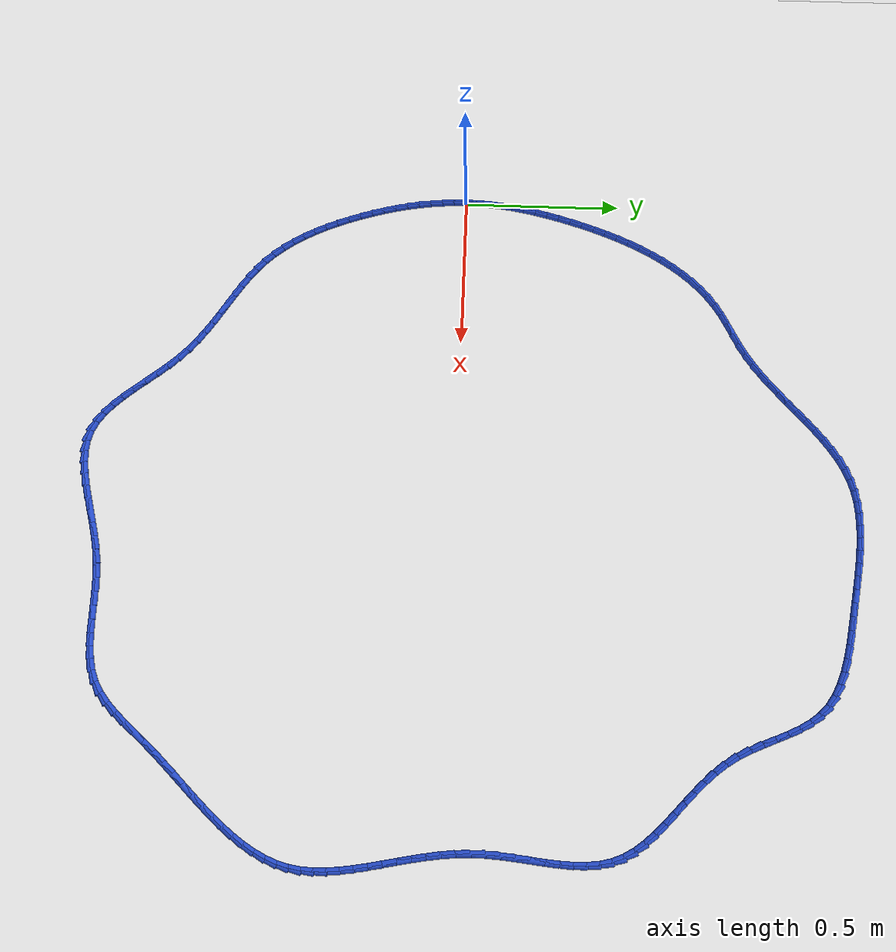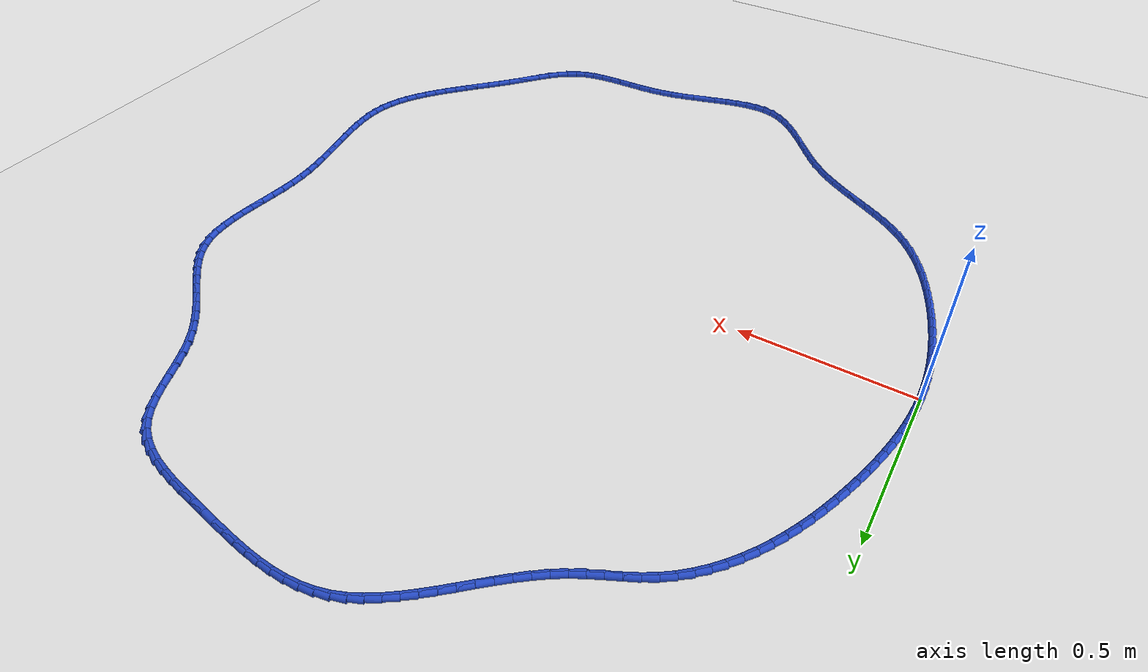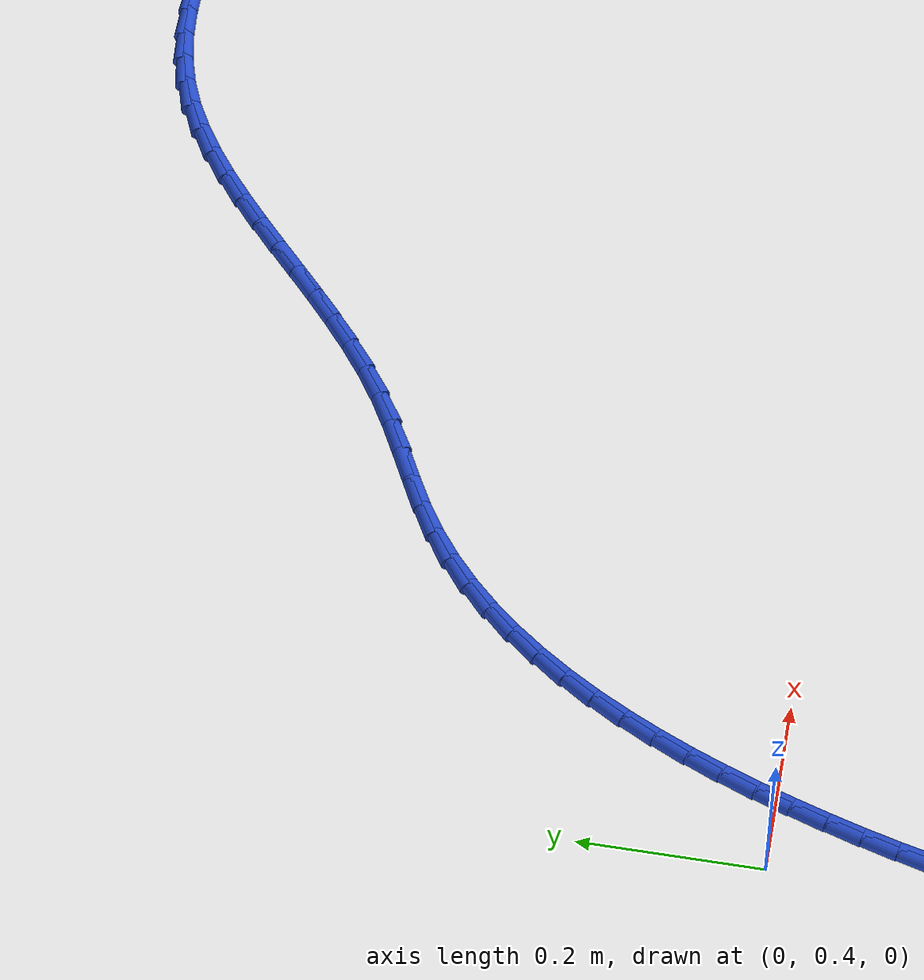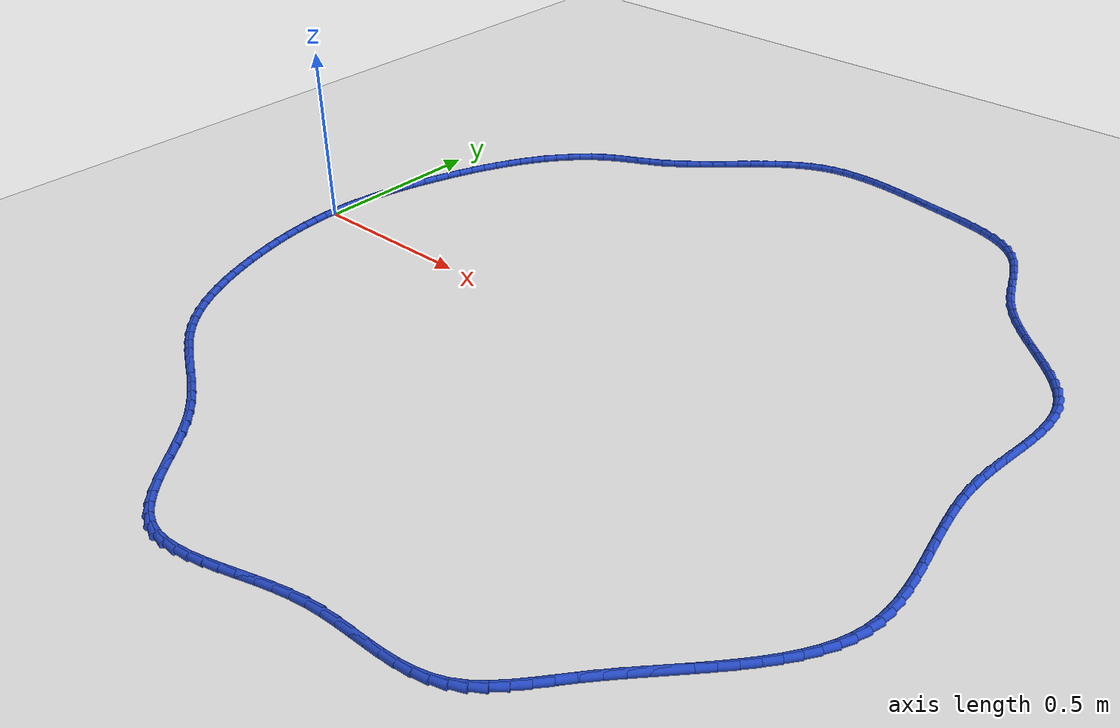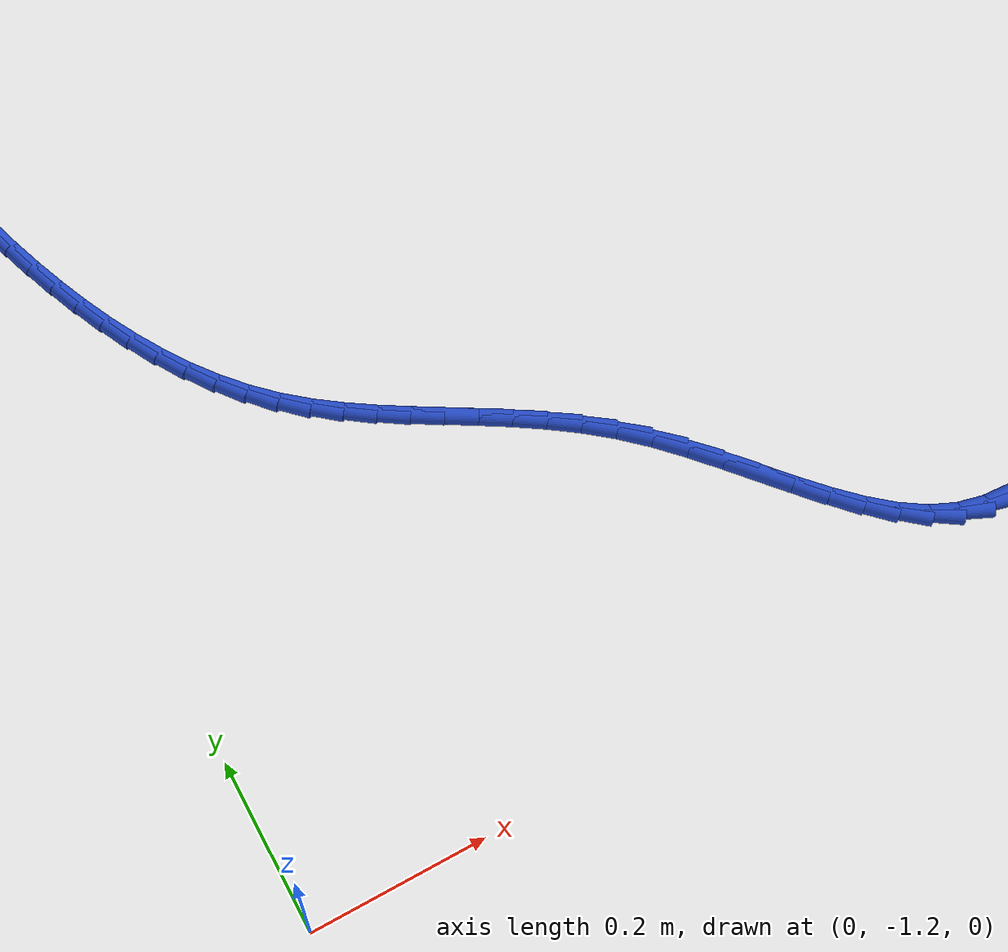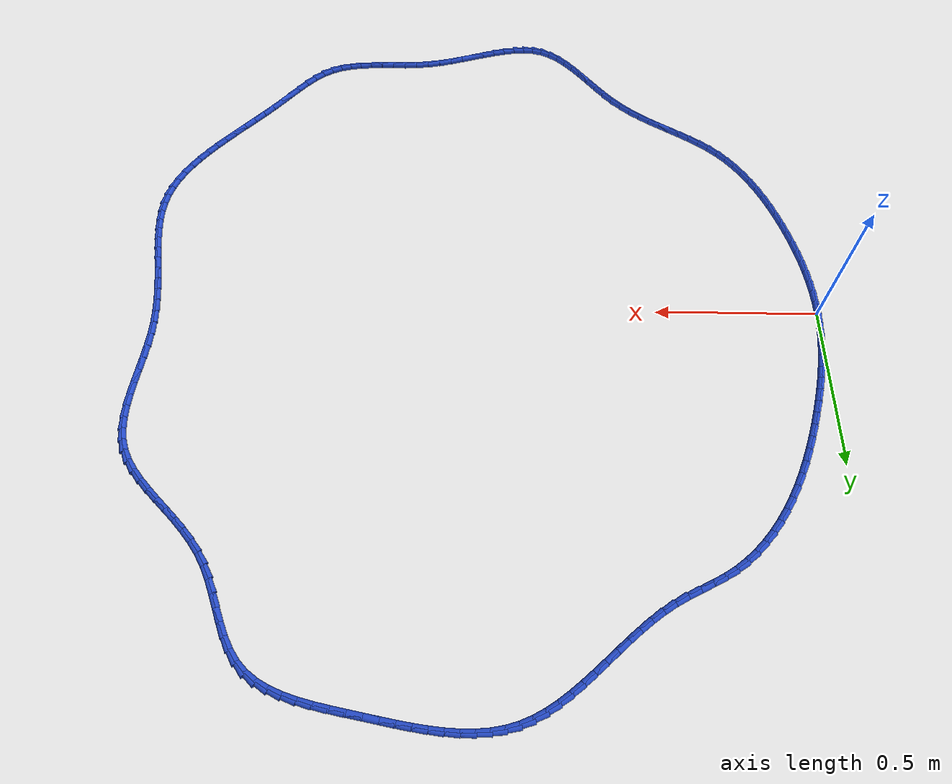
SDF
<sdf version="1.6">
 <world name="default">
  <light name="sun" type="directional">
   <pose>0 0 10 0 -0 0</pose>
   <diffuse>0.8 0.8 0.8 1</diffuse>
   <specular>0.2 0.2 0.2 1</specular>
   <attenuation>
    <range>1000</range>
    <constant>0.9</constant>
    <linear>0.01</linear>
    <quadratic>0.001</quadratic>
   </attenuation>
   <direction>-0.5 0.1 -0.9</direction>
  </light>
  <model name="ground_plane">
   <static>1</static>
   <link name="link">
    <collision name="collision">
     <geometry><plane><normal>0 0 1</normal><size>100 100</size></plane></geometry>
     <surface><friction><ode><mu>100</mu><mu2>50</mu2></ode></friction></surface>
    </collision>
    <visual name="visual">
     <cast_shadows>0</cast_shadows>
     <geometry><plane><normal>0 0 1</normal><size>100 100</size></plane></geometry>
     <material>
      <script><uri>file://media/materials/scripts/gazebo.material</uri><name>Gazebo/WhiteGlow</name></script>
     </material>
    </visual>
   </link>
  </model>
  <gravity>0 0 -9.8</gravity>
  <magnetic_field>6e-06 2.3e-05 -4.2e-05</magnetic_field>
  <atmosphere type="adiabatic"/>
  <physics name="default_physics" default="0" type="ode">
   <max_step_size>0.001</max_step_size>
   <real_time_factor>1</real_time_factor>
   <real_time_update_rate>1000</real_time_update_rate>
  </physics>
  <scene><ambient>0.4 0.4 0.4 1</ambient><background>0.7 0.7 0.7 1</background><shadows>1</shadows></scene>
  <spherical_coordinates>
   <surface_model>EARTH_WGS84</surface_model>
   <latitude_deg>0</latitude_deg>
   <longitude_deg>0</longitude_deg>
   <elevation>0</elevation>
   <heading_deg>0</heading_deg>
  </spherical_coordinates>
  <model name="line">
   <link name="link_0">
    <pose>5.204170427930421e-18 -4.85722573273506e-17 0.01 0 1.57 1.5430698110290437</pose>
    <collision name="collision">
     <geometry><cylinder><radius>0.01</radius><length>0.08</length></cylinder></geometry>
    </collision>
    <visual name="visual">
     <material>
      <script><name>Gazebo/Blue</name><uri>file://media/materials/scripts/gazebo.material</uri></script>
     </material>
     <geometry><cylinder><radius>0.01</radius><length>0.08</length></cylinder></geometry>
    </visual>
   </link>
   <link name="link_1">
    <pose>0.0010610691072899844 0.038259303835031455 0.01 0 1.57 1.4999018727812456</pose>
    <collision name="collision">
     <geometry><cylinder><radius>0.01</radius><length>0.08</length></cylinder></geometry>
    </collision>
    <visual name="visual">
     <material>
      <script><name>Gazebo/Blue</name><uri>file://media/materials/scripts/gazebo.material</uri></script>
     </material>
     <geometry><cylinder><radius>0.01</radius><length>0.08</length></cylinder></geometry>
    </visual>
   </link>
   <link name="link_2">
    <pose>0.003774505061248298 0.07646946479422213 0.01 0 1.57 1.459412078133908</pose>
    <collision name="collision">
     <geometry><cylinder><radius>0.01</radius><length>0.08</length></cylinder></geometry>
    </collision>
    <visual name="visual">
     <material>
      <script><name>Gazebo/Blue</name><uri>file://media/materials/scripts/gazebo.material</uri></script>
     </material>
     <geometry><cylinder><radius>0.01</radius><length>0.08</length></cylinder></geometry>
    </visual>
   </link>
   <link name="link_3">
    <pose>0.008045083456441992 0.11465172947503895 0.01 0 1.57 1.421748723138477</pose>
    <collision name="collision">
     <geometry><cylinder><radius>0.01</radius><length>0.08</length></cylinder></geometry>
    </collision>
    <visual name="visual">
     <material>
      <script><name>Gazebo/Blue</name><uri>file://media/materials/scripts/gazebo.material</uri></script>
     </material>
     <geometry><cylinder><radius>0.01</radius><length>0.08</length></cylinder></geometry>
    </visual>
   </link>
   <link name="link_4">
    <pose>0.01377757988743812 0.1528273444749488 0.01 0 1.57 1.3870038572048446</pose>
    <collision name="collision">
     <geometry><cylinder><radius>0.01</radius><length>0.08</length></cylinder></geometry>
    </collision>
    <visual name="visual">
     <material>
      <script><name>Gazebo/Blue</name><uri>file://media/materials/scripts/gazebo.material</uri></script>
     </material>
     <geometry><cylinder><radius>0.01</radius><length>0.08</length></cylinder></geometry>
    </visual>
   </link>
   <link name="link_5">
    <pose>0.020876769948803737 0.1910175563914186 0.01 0 1.57 1.3552211961631595</pose>
    <collision name="collision">
     <geometry><cylinder><radius>0.01</radius><length>0.08</length></cylinder></geometry>
    </collision>
    <visual name="visual">
     <material>
      <script><name>Gazebo/Blue</name><uri>file://media/materials/scripts/gazebo.material</uri></script>
     </material>
     <geometry><cylinder><radius>0.01</radius><length>0.08</length></cylinder></geometry>
    </visual>
   </link>
   <link name="link_6">
    <pose>0.0292474292351059 0.22924361182191547 0.01 0 1.57 1.326404886494803</pose>
    <collision name="collision">
     <geometry><cylinder><radius>0.01</radius><length>0.08</length></cylinder></geometry>
    </collision>
    <visual name="visual">
     <material>
      <script><name>Gazebo/Blue</name><uri>file://media/materials/scripts/gazebo.material</uri></script>
     </material>
     <geometry><cylinder><radius>0.01</radius><length>0.08</length></cylinder></geometry>
    </visual>
   </link>
   <link name="link_7">
    <pose>0.03879433334091166 0.26752675736390624 0.01 0 1.57 1.300528253204703</pose>
    <collision name="collision">
     <geometry><cylinder><radius>0.01</radius><length>0.08</length></cylinder></geometry>
    </collision>
    <visual name="visual">
     <material>
      <script><name>Gazebo/Blue</name><uri>file://media/materials/scripts/gazebo.material</uri></script>
     </material>
     <geometry><cylinder><radius>0.01</radius><length>0.08</length></cylinder></geometry>
    </visual>
   </link>
   <link name="link_8">
    <pose>0.04942225786078808 0.3058882396148579 0.01 0 1.57 1.2775417288491522</pose>
    <collision name="collision">
     <geometry><cylinder><radius>0.01</radius><length>0.08</length></cylinder></geometry>
    </collision>
    <visual name="visual">
     <material>
      <script><name>Gazebo/Blue</name><uri>file://media/materials/scripts/gazebo.material</uri></script>
     </material>
     <geometry><cylinder><radius>0.01</radius><length>0.08</length></cylinder></geometry>
    </visual>
   </link>
   <link name="link_9">
    <pose>0.061035984458575575 0.34434929739520004 0.01 0 1.57 1.2562940148241608</pose>
    <collision name="collision">
     <geometry><cylinder><radius>0.01</radius><length>0.08</length></cylinder></geometry>
    </collision>
    <visual name="visual">
     <material>
      <script><name>Gazebo/Blue</name><uri>file://media/materials/scripts/gazebo.material</uri></script>
     </material>
     <geometry><cylinder><radius>0.01</radius><length>0.08</length></cylinder></geometry>
    </visual>
   </link>
   <link name="link_10">
    <pose>0.07357299745309168 0.38288926504176707 0.01 0 1.57 1.2330434593282864</pose>
    <collision name="collision">
     <geometry><cylinder><radius>0.01</radius><length>0.08</length></cylinder></geometry>
    </collision>
    <visual name="visual">
     <material>
      <script><name>Gazebo/Blue</name><uri>file://media/materials/scripts/gazebo.material</uri></script>
     </material>
     <geometry><cylinder><radius>0.01</radius><length>0.08</length></cylinder></geometry>
    </visual>
   </link>
   <link name="link_11">
    <pose>0.08707996216094537 0.4213475746928076 0.01 0 1.57 1.2068416024750563</pose>
    <collision name="collision">
     <geometry><cylinder><radius>0.01</radius><length>0.08</length></cylinder></geometry>
    </collision>
    <visual name="visual">
     <material>
      <script><name>Gazebo/Blue</name><uri>file://media/materials/scripts/gazebo.material</uri></script>
     </material>
     <geometry><cylinder><radius>0.01</radius><length>0.08</length></cylinder></geometry>
    </visual>
   </link>
   <link name="link_12">
    <pose>0.10162630159828318 0.4595344972564615 0.01 0 1.57 1.17745041678698</pose>
    <collision name="collision">
     <geometry><cylinder><radius>0.01</radius><length>0.08</length></cylinder></geometry>
    </collision>
    <visual name="visual">
     <material>
      <script><name>Gazebo/Blue</name><uri>file://media/materials/scripts/gazebo.material</uri></script>
     </material>
     <geometry><cylinder><radius>0.01</radius><length>0.08</length></cylinder></geometry>
    </visual>
   </link>
   <link name="link_13">
    <pose>0.11728143878125181 0.4972603036408692 0.01 0 1.57 1.1445913373499985</pose>
    <collision name="collision">
     <geometry><cylinder><radius>0.01</radius><length>0.08</length></cylinder></geometry>
    </collision>
    <visual name="visual">
     <material>
      <script><name>Gazebo/Blue</name><uri>file://media/materials/scripts/gazebo.material</uri></script>
     </material>
     <geometry><cylinder><radius>0.01</radius><length>0.08</length></cylinder></geometry>
    </visual>
   </link>
   <link name="link_14">
    <pose>0.13411479672599777 0.5343352647541708 0.01 0 1.57 1.1079480934899388</pose>
    <collision name="collision">
     <geometry><cylinder><radius>0.01</radius><length>0.08</length></cylinder></geometry>
    </collision>
    <visual name="visual">
     <material>
      <script><name>Gazebo/Blue</name><uri>file://media/materials/scripts/gazebo.material</uri></script>
     </material>
     <geometry><cylinder><radius>0.01</radius><length>0.08</length></cylinder></geometry>
    </visual>
   </link>
   <link name="link_15">
    <pose>0.1521957984486677 0.5705696515045064 0.01 0 1.57 1.0671722059517301</pose>
    <collision name="collision">
     <geometry><cylinder><radius>0.01</radius><length>0.08</length></cylinder></geometry>
    </collision>
    <visual name="visual">
     <material>
      <script><name>Gazebo/Blue</name><uri>file://media/materials/scripts/gazebo.material</uri></script>
     </material>
     <geometry><cylinder><radius>0.01</radius><length>0.08</length></cylinder></geometry>
    </visual>
   </link>
   <link name="link_16">
    <pose>0.17159386696540813 0.6057737348000165 0.01 0 1.57 1.0218929122133151</pose>
    <collision name="collision">
     <geometry><cylinder><radius>0.01</radius><length>0.08</length></cylinder></geometry>
    </collision>
    <visual name="visual">
     <material>
      <script><name>Gazebo/Blue</name><uri>file://media/materials/scripts/gazebo.material</uri></script>
     </material>
     <geometry><cylinder><radius>0.01</radius><length>0.08</length></cylinder></geometry>
    </visual>
   </link>
   <link name="link_17">
    <pose>0.19237842529236565 0.6397577855488406 0.01 0 1.57 0.9717337445342652</pose>
    <collision name="collision">
     <geometry><cylinder><radius>0.01</radius><length>0.08</length></cylinder></geometry>
    </collision>
    <visual name="visual">
     <material>
      <script><name>Gazebo/Blue</name><uri>file://media/materials/scripts/gazebo.material</uri></script>
     </material>
     <geometry><cylinder><radius>0.01</radius><length>0.08</length></cylinder></geometry>
    </visual>
   </link>
   <link name="link_18">
    <pose>0.2146188964456869 0.6723320746591194 0.01 0 1.57 0.9163383309825583</pose>
    <collision name="collision">
     <geometry><cylinder><radius>0.01</radius><length>0.08</length></cylinder></geometry>
    </collision>
    <visual name="visual">
     <material>
      <script><name>Gazebo/Blue</name><uri>file://media/materials/scripts/gazebo.material</uri></script>
     </material>
     <geometry><cylinder><radius>0.01</radius><length>0.08</length></cylinder></geometry>
    </visual>
   </link>
   <link name="link_19">
    <pose>0.23838470344151846 0.7033068730389929 0.01 0 1.57 0.8554079036243049</pose>
    <collision name="collision">
     <geometry><cylinder><radius>0.01</radius><length>0.08</length></cylinder></geometry>
    </collision>
    <visual name="visual">
     <material>
      <script><name>Gazebo/Blue</name><uri>file://media/materials/scripts/gazebo.material</uri></script>
     </material>
     <geometry><cylinder><radius>0.01</radius><length>0.08</length></cylinder></geometry>
    </visual>
   </link>
   <link name="link_20">
    <pose>0.263745269296007 0.7324924515966011 0.01 0 1.57 0.7887519641133337</pose>
    <collision name="collision">
     <geometry><cylinder><radius>0.01</radius><length>0.08</length></cylinder></geometry>
    </collision>
    <visual name="visual">
     <material>
      <script><name>Gazebo/Blue</name><uri>file://media/materials/scripts/gazebo.material</uri></script>
     </material>
     <geometry><cylinder><radius>0.01</radius><length>0.08</length></cylinder></geometry>
    </visual>
   </link>
   <link name="link_21">
    <pose>0.29077001702529887 0.7596990812400845 0.01 0 1.57 0.7163509158405015</pose>
    <collision name="collision">
     <geometry><cylinder><radius>0.01</radius><length>0.08</length></cylinder></geometry>
    </collision>
    <visual name="visual">
     <material>
      <script><name>Gazebo/Blue</name><uri>file://media/materials/scripts/gazebo.material</uri></script>
     </material>
     <geometry><cylinder><radius>0.01</radius><length>0.08</length></cylinder></geometry>
    </visual>
   </link>
   <link name="link_22">
    <pose>0.31952836964554093 0.7847370328775829 0.01 0 1.57 0.6384247264630082</pose>
    <collision name="collision">
     <geometry><cylinder><radius>0.01</radius><length>0.08</length></cylinder></geometry>
    </collision>
    <visual name="visual">
     <material>
      <script><name>Gazebo/Blue</name><uri>file://media/materials/scripts/gazebo.material</uri></script>
     </material>
     <geometry><cylinder><radius>0.01</radius><length>0.08</length></cylinder></geometry>
    </visual>
   </link>
   <link name="link_23">
    <pose>0.3500897501728797 0.8074165774172368 0.01 0 1.57 0.5564719035018222</pose>
    <collision name="collision">
     <geometry><cylinder><radius>0.01</radius><length>0.08</length></cylinder></geometry>
    </collision>
    <visual name="visual">
     <material>
      <script><name>Gazebo/Blue</name><uri>file://media/materials/scripts/gazebo.material</uri></script>
     </material>
     <geometry><cylinder><radius>0.01</radius><length>0.08</length></cylinder></geometry>
    </visual>
   </link>
   <link name="link_24">
    <pose>0.3825052597876371 0.8275804990394438 0.01 0 1.57 0.4914078962530424</pose>
    <collision name="collision">
     <geometry><cylinder><radius>0.01</radius><length>0.08</length></cylinder></geometry>
    </collision>
    <visual name="visual">
     <material>
      <script><name>Gazebo/Blue</name><uri>file://media/materials/scripts/gazebo.material</uri></script>
     </material>
     <geometry><cylinder><radius>0.01</radius><length>0.08</length></cylinder></geometry>
    </visual>
   </link>
   <link name="link_25">
    <pose>0.4164461740224169 0.8457456068865743 0.01 0 1.57 0.46200758105183815</pose>
    <collision name="collision">
     <geometry><cylinder><radius>0.01</radius><length>0.08</length></cylinder></geometry>
    </collision>
    <visual name="visual">
     <material>
      <script><name>Gazebo/Blue</name><uri>file://media/materials/scripts/gazebo.material</uri></script>
     </material>
     <geometry><cylinder><radius>0.01</radius><length>0.08</length></cylinder></geometry>
    </visual>
   </link>
   <link name="link_26">
    <pose>0.4512256984434859 0.8630641282116305 0.01 0 1.57 0.46799715615209214</pose>
    <collision name="collision">
     <geometry><cylinder><radius>0.01</radius><length>0.08</length></cylinder></geometry>
    </collision>
    <visual name="visual">
     <material>
      <script><name>Gazebo/Blue</name><uri>file://media/materials/scripts/gazebo.material</uri></script>
     </material>
     <geometry><cylinder><radius>0.01</radius><length>0.08</length></cylinder></geometry>
    </visual>
   </link>
   <link name="link_27">
    <pose>0.4861430726636016 0.8807130737474538 0.01 0 1.57 0.5086645691222513</pose>
    <collision name="collision">
     <geometry><cylinder><radius>0.01</radius><length>0.08</length></cylinder></geometry>
    </collision>
    <visual name="visual">
     <material>
      <script><name>Gazebo/Blue</name><uri>file://media/materials/scripts/gazebo.material</uri></script>
     </material>
     <geometry><cylinder><radius>0.01</radius><length>0.08</length></cylinder></geometry>
    </visual>
   </link>
   <link name="link_28">
    <pose>0.5204975769959039 0.8998693775960086 0.01 0 1.57 0.5738189195218272</pose>
    <collision name="collision">
     <geometry><cylinder><radius>0.01</radius><length>0.08</length></cylinder></geometry>
    </collision>
    <visual name="visual">
     <material>
      <script><name>Gazebo/Blue</name><uri>file://media/materials/scripts/gazebo.material</uri></script>
     </material>
     <geometry><cylinder><radius>0.01</radius><length>0.08</length></cylinder></geometry>
    </visual>
   </link>
   <link name="link_29">
    <pose>0.5537670607159184 0.9213737633393478 0.01 0 1.57 0.6314462953508727</pose>
    <collision name="collision">
     <geometry><cylinder><radius>0.01</radius><length>0.08</length></cylinder></geometry>
    </collision>
    <visual name="visual">
     <material>
      <script><name>Gazebo/Blue</name><uri>file://media/materials/scripts/gazebo.material</uri></script>
     </material>
     <geometry><cylinder><radius>0.01</radius><length>0.08</length></cylinder></geometry>
    </visual>
   </link>
   <link name="link_30">
    <pose>0.5860175296135585 0.9449595705839011 0.01 0 1.57 0.6754819135691965</pose>
    <collision name="collision">
     <geometry><cylinder><radius>0.01</radius><length>0.08</length></cylinder></geometry>
    </collision>
    <visual name="visual">
     <material>
      <script><name>Gazebo/Blue</name><uri>file://media/materials/scripts/gazebo.material</uri></script>
     </material>
     <geometry><cylinder><radius>0.01</radius><length>0.08</length></cylinder></geometry>
    </visual>
   </link>
   <link name="link_31">
    <pose>0.6174359071099166 0.9701324746258959 0.01 0 1.57 0.7065364346487866</pose>
    <collision name="collision">
     <geometry><cylinder><radius>0.01</radius><length>0.08</length></cylinder></geometry>
    </collision>
    <visual name="visual">
     <material>
      <script><name>Gazebo/Blue</name><uri>file://media/materials/scripts/gazebo.material</uri></script>
     </material>
     <geometry><cylinder><radius>0.01</radius><length>0.08</length></cylinder></geometry>
    </visual>
   </link>
   <link name="link_32">
    <pose>0.6482091166260855 0.9963981507615602 0.01 0 1.57 0.7251198170612014</pose>
    <collision name="collision">
     <geometry><cylinder><radius>0.01</radius><length>0.08</length></cylinder></geometry>
    </collision>
    <visual name="visual">
     <material>
      <script><name>Gazebo/Blue</name><uri>file://media/materials/scripts/gazebo.material</uri></script>
     </material>
     <geometry><cylinder><radius>0.01</radius><length>0.08</length></cylinder></geometry>
    </visual>
   </link>
   <link name="link_33">
    <pose>0.6785240815831581 1.0232622742871216 0.01 0 1.57 0.7315073028463244</pose>
    <collision name="collision">
     <geometry><cylinder><radius>0.01</radius><length>0.08</length></cylinder></geometry>
    </collision>
    <visual name="visual">
     <material>
      <script><name>Gazebo/Blue</name><uri>file://media/materials/scripts/gazebo.material</uri></script>
     </material>
     <geometry><cylinder><radius>0.01</radius><length>0.08</length></cylinder></geometry>
    </visual>
   </link>
   <link name="link_34">
    <pose>0.7085677254022268 1.0502305204988078 0.01 0 1.57 0.7256645003087803</pose>
    <collision name="collision">
     <geometry><cylinder><radius>0.01</radius><length>0.08</length></cylinder></geometry>
    </collision>
    <visual name="visual">
     <material>
      <script><name>Gazebo/Blue</name><uri>file://media/materials/scripts/gazebo.material</uri></script>
     </material>
     <geometry><cylinder><radius>0.01</radius><length>0.08</length></cylinder></geometry>
    </visual>
   </link>
   <link name="link_35">
    <pose>0.7385269715043844 1.0768085646928467 0.01 0 1.57 0.707210974886828</pose>
    <collision name="collision">
     <geometry><cylinder><radius>0.01</radius><length>0.08</length></cylinder></geometry>
    </collision>
    <visual name="visual">
     <material>
      <script><name>Gazebo/Blue</name><uri>file://media/materials/scripts/gazebo.material</uri></script>
     </material>
     <geometry><cylinder><radius>0.01</radius><length>0.08</length></cylinder></geometry>
    </visual>
   </link>
   <link name="link_36">
    <pose>0.7685887433107235 1.102502082165466 0.01 0 1.57 0.6754173940089991</pose>
    <collision name="collision">
     <geometry><cylinder><radius>0.01</radius><length>0.08</length></cylinder></geometry>
    </collision>
    <visual name="visual">
     <material>
      <script><name>Gazebo/Blue</name><uri>file://media/materials/scripts/gazebo.material</uri></script>
     </material>
     <geometry><cylinder><radius>0.01</radius><length>0.08</length></cylinder></geometry>
    </visual>
   </link>
   <link name="link_37">
    <pose>0.798939964242337 1.1268167482128935 0.01 0 1.57 0.6292506349643531</pose>
    <collision name="collision">
     <geometry><cylinder><radius>0.01</radius><length>0.08</length></cylinder></geometry>
    </collision>
    <visual name="visual">
     <material>
      <script><name>Gazebo/Blue</name><uri>file://media/materials/scripts/gazebo.material</uri></script>
     </material>
     <geometry><cylinder><radius>0.01</radius><length>0.08</length></cylinder></geometry>
    </visual>
   </link>
   <link name="link_38">
    <pose>0.8297675577203169 1.1492582381313563 0.01 0 1.57 0.5675048182941815</pose>
    <collision name="collision">
     <geometry><cylinder><radius>0.01</radius><length>0.08</length></cylinder></geometry>
    </collision>
    <visual name="visual">
     <material>
      <script><name>Gazebo/Blue</name><uri>file://media/materials/scripts/gazebo.material</uri></script>
     </material>
     <geometry><cylinder><radius>0.01</radius><length>0.08</length></cylinder></geometry>
    </visual>
   </link>
   <link name="link_39">
    <pose>0.8612584471657567 1.1693322272170834 0.01 0 1.57 0.48907998992968993</pose>
    <collision name="collision">
     <geometry><cylinder><radius>0.01</radius><length>0.08</length></cylinder></geometry>
    </collision>
    <visual name="visual">
     <material>
      <script><name>Gazebo/Blue</name><uri>file://media/materials/scripts/gazebo.material</uri></script>
     </material>
     <geometry><cylinder><radius>0.01</radius><length>0.08</length></cylinder></geometry>
    </visual>
   </link>
   <link name="link_40">
    <pose>0.8935995559997485 1.1865443907663011 0.01 0 1.57 0.3934733823606652</pose>
    <collision name="collision">
     <geometry><cylinder><radius>0.01</radius><length>0.08</length></cylinder></geometry>
    </collision>
    <visual name="visual">
     <material>
      <script><name>Gazebo/Blue</name><uri>file://media/materials/scripts/gazebo.material</uri></script>
     </material>
     <geometry><cylinder><radius>0.01</radius><length>0.08</length></cylinder></geometry>
    </visual>
   </link>
   <link name="link_41">
    <pose>0.926977807643385 1.2004004040752383 0.01 0 1.57 0.2845085435991774</pose>
    <collision name="collision">
     <geometry><cylinder><radius>0.01</radius><length>0.08</length></cylinder></geometry>
    </collision>
    <visual name="visual">
     <material>
      <script><name>Gazebo/Blue</name><uri>file://media/materials/scripts/gazebo.material</uri></script>
     </material>
     <geometry><cylinder><radius>0.01</radius><length>0.08</length></cylinder></geometry>
    </visual>
   </link>
   <link name="link_42">
    <pose>0.9615470079958154 1.2105098915231263 0.01 0 1.57 0.18145552733307635</pose>
    <collision name="collision">
     <geometry><cylinder><radius>0.01</radius><length>0.08</length></cylinder></geometry>
    </collision>
    <visual name="visual">
     <material>
      <script><name>Gazebo/Blue</name><uri>file://media/materials/scripts/gazebo.material</uri></script>
     </material>
     <geometry><cylinder><radius>0.01</radius><length>0.08</length></cylinder></geometry>
    </visual>
   </link>
   <link name="link_43">
    <pose>0.9972753432013762 1.2170650996833543 0.01 0 1.57 0.09204527545631257</pose>
    <collision name="collision">
     <geometry><cylinder><radius>0.01</radius><length>0.08</length></cylinder></geometry>
    </collision>
    <visual name="visual">
     <material>
      <script><name>Gazebo/Blue</name><uri>file://media/materials/scripts/gazebo.material</uri></script>
     </material>
     <geometry><cylinder><radius>0.01</radius><length>0.08</length></cylinder></geometry>
    </visual>
   </link>
   <link name="link_44">
    <pose>1.0340663692074799 1.2204611360111166 0.01 0 1.57 0.016741684028600965</pose>
    <collision name="collision">
     <geometry><cylinder><radius>0.01</radius><length>0.08</length></cylinder></geometry>
    </collision>
    <visual name="visual">
     <material>
      <script><name>Gazebo/Blue</name><uri>file://media/materials/scripts/gazebo.material</uri></script>
     </material>
     <geometry><cylinder><radius>0.01</radius><length>0.08</length></cylinder></geometry>
    </visual>
   </link>
   <link name="link_45">
    <pose>1.0718235762218329 1.2210933143050073 0.01 0 1.57 -0.04492203032472835</pose>
    <collision name="collision">
     <geometry><cylinder><radius>0.01</radius><length>0.08</length></cylinder></geometry>
    </collision>
    <visual name="visual">
     <material>
      <script><name>Gazebo/Blue</name><uri>file://media/materials/scripts/gazebo.material</uri></script>
     </material>
     <geometry><cylinder><radius>0.01</radius><length>0.08</length></cylinder></geometry>
    </visual>
   </link>
   <link name="link_46">
    <pose>1.1104504544521419 1.2193569483636206 0.01 0 1.57 -0.0938753605507853</pose>
    <collision name="collision">
     <geometry><cylinder><radius>0.01</radius><length>0.08</length></cylinder></geometry>
    </collision>
    <visual name="visual">
     <material>
      <script><name>Gazebo/Blue</name><uri>file://media/materials/scripts/gazebo.material</uri></script>
     </material>
     <geometry><cylinder><radius>0.01</radius><length>0.08</length></cylinder></geometry>
    </visual>
   </link>
   <link name="link_47">
    <pose>1.1498504941061134 1.2156473519855513 0.01 0 1.57 -0.13117724441278245</pose>
    <collision name="collision">
     <geometry><cylinder><radius>0.01</radius><length>0.08</length></cylinder></geometry>
    </collision>
    <visual name="visual">
     <material>
      <script><name>Gazebo/Blue</name><uri>file://media/materials/scripts/gazebo.material</uri></script>
     </material>
     <geometry><cylinder><radius>0.01</radius><length>0.08</length></cylinder></geometry>
    </visual>
   </link>
   <link name="link_48">
    <pose>1.1899271853914535 1.210359838969393 0.01 0 1.57 -0.1578163148414161</pose>
    <collision name="collision">
     <geometry><cylinder><radius>0.01</radius><length>0.08</length></cylinder></geometry>
    </collision>
    <visual name="visual">
     <material>
      <script><name>Gazebo/Blue</name><uri>file://media/materials/scripts/gazebo.material</uri></script>
     </material>
     <geometry><cylinder><radius>0.01</radius><length>0.08</length></cylinder></geometry>
    </visual>
   </link>
   <link name="link_49">
    <pose>1.2305840185158705 1.2038897231137407 0.01 0 1.57 -0.17460908920680784</pose>
    <collision name="collision">
     <geometry><cylinder><radius>0.01</radius><length>0.08</length></cylinder></geometry>
    </collision>
    <visual name="visual">
     <material>
      <script><name>Gazebo/Blue</name><uri>file://media/materials/scripts/gazebo.material</uri></script>
     </material>
     <geometry><cylinder><radius>0.01</radius><length>0.08</length></cylinder></geometry>
    </visual>
   </link>
   <link name="link_50">
    <pose>1.2717244836870691 1.1966323182171879 0.01 0 1.57 -0.18215809549075143</pose>
    <collision name="collision">
     <geometry><cylinder><radius>0.01</radius><length>0.08</length></cylinder></geometry>
    </collision>
    <visual name="visual">
     <material>
      <script><name>Gazebo/Blue</name><uri>file://media/materials/scripts/gazebo.material</uri></script>
     </material>
     <geometry><cylinder><radius>0.01</radius><length>0.08</length></cylinder></geometry>
    </visual>
   </link>
   <link name="link_51">
    <pose>1.3132520711127573 1.1889829380783292 0.01 0 1.57 -0.18146093318876846</pose>
    <collision name="collision">
     <geometry><cylinder><radius>0.01</radius><length>0.08</length></cylinder></geometry>
    </collision>
    <visual name="visual">
     <material>
      <script><name>Gazebo/Blue</name><uri>file://media/materials/scripts/gazebo.material</uri></script>
     </material>
     <geometry><cylinder><radius>0.01</radius><length>0.08</length></cylinder></geometry>
    </visual>
   </link>
   <link name="link_52">
    <pose>1.3550585231241778 1.1813123220194042 0.01 0 1.57 -0.1848133084151161</pose>
    <collision name="collision">
     <geometry><cylinder><radius>0.01</radius><length>0.08</length></cylinder></geometry>
    </collision>
    <visual name="visual">
     <material>
      <script><name>Gazebo/Blue</name><uri>file://media/materials/scripts/gazebo.material</uri></script>
     </material>
     <geometry><cylinder><radius>0.01</radius><length>0.08</length></cylinder></geometry>
    </visual>
   </link>
   <link name="link_53">
    <pose>1.3968045992586018 1.1735080342776658 0.01 0 1.57 -0.20357956919629636</pose>
    <collision name="collision">
     <geometry><cylinder><radius>0.01</radius><length>0.08</length></cylinder></geometry>
    </collision>
    <visual name="visual">
     <material>
      <script><name>Gazebo/Blue</name><uri>file://media/materials/scripts/gazebo.material</uri></script>
     </material>
     <geometry><cylinder><radius>0.01</radius><length>0.08</length></cylinder></geometry>
    </visual>
   </link>
   <link name="link_54">
    <pose>1.437939967465345 1.165016072884515 0.01 0 1.57 -0.23927705951594538</pose>
    <collision name="collision">
     <geometry><cylinder><radius>0.01</radius><length>0.08</length></cylinder></geometry>
    </collision>
    <visual name="visual">
     <material>
      <script><name>Gazebo/Blue</name><uri>file://media/materials/scripts/gazebo.material</uri></script>
     </material>
     <geometry><cylinder><radius>0.01</radius><length>0.08</length></cylinder></geometry>
    </visual>
   </link>
   <link name="link_55">
    <pose>1.477906536174173 1.1552662043310993 0.01 0 1.57 -0.2940004978064411</pose>
    <collision name="collision">
     <geometry><cylinder><radius>0.01</radius><length>0.08</length></cylinder></geometry>
    </collision>
    <visual name="visual">
     <material>
      <script><name>Gazebo/Blue</name><uri>file://media/materials/scripts/gazebo.material</uri></script>
     </material>
     <geometry><cylinder><radius>0.01</radius><length>0.08</length></cylinder></geometry>
    </visual>
   </link>
   <link name="link_56">
    <pose>1.5161462138148498 1.1436881951085685 0.01 0 1.57 -0.3707463746853357</pose>
    <collision name="collision">
     <geometry><cylinder><radius>0.01</radius><length>0.08</length></cylinder></geometry>
    </collision>
    <visual name="visual">
     <material>
      <script><name>Gazebo/Blue</name><uri>file://media/materials/scripts/gazebo.material</uri></script>
     </material>
     <geometry><cylinder><radius>0.01</radius><length>0.08</length></cylinder></geometry>
    </visual>
   </link>
   <link name="link_57">
    <pose>1.552100908817142 1.12971181170807 0.01 0 1.57 -0.47300621422693206</pose>
    <collision name="collision">
     <geometry><cylinder><radius>0.01</radius><length>0.08</length></cylinder></geometry>
    </collision>
    <visual name="visual">
     <material>
      <script><name>Gazebo/Blue</name><uri>file://media/materials/scripts/gazebo.material</uri></script>
     </material>
     <geometry><cylinder><radius>0.01</radius><length>0.08</length></cylinder></geometry>
    </visual>
   </link>
   <link name="link_58">
    <pose>1.585212529610816 1.1127668206207537 0.01 0 1.57 -0.6036093452666672</pose>
    <collision name="collision">
     <geometry><cylinder><radius>0.01</radius><length>0.08</length></cylinder></geometry>
    </collision>
    <visual name="visual">
     <material>
      <script><name>Gazebo/Blue</name><uri>file://media/materials/scripts/gazebo.material</uri></script>
     </material>
     <geometry><cylinder><radius>0.01</radius><length>0.08</length></cylinder></geometry>
    </visual>
   </link>
   <link name="link_59">
    <pose>1.6149229846256352 1.092282988337768 0.01 0 1.57 -0.7622111997289494</pose>
    <collision name="collision">
     <geometry><cylinder><radius>0.01</radius><length>0.08</length></cylinder></geometry>
    </collision>
    <visual name="visual">
     <material>
      <script><name>Gazebo/Blue</name><uri>file://media/materials/scripts/gazebo.material</uri></script>
     </material>
     <geometry><cylinder><radius>0.01</radius><length>0.08</length></cylinder></geometry>
    </visual>
   </link>
   <link name="link_60">
    <pose>1.6406790133723932 1.0676945052042912 0.01 0 1.57 -0.9235636580012856</pose>
    <collision name="collision">
     <geometry><cylinder><radius>0.01</radius><length>0.08</length></cylinder></geometry>
    </collision>
    <visual name="visual">
     <material>
      <script><name>Gazebo/Blue</name><uri>file://media/materials/scripts/gazebo.material</uri></script>
     </material>
     <geometry><cylinder><radius>0.01</radius><length>0.08</length></cylinder></geometry>
    </visual>
   </link>
   <link name="link_61">
    <pose>1.6624396914387491 1.0389047112249352 0.01 0 1.57 -1.0451921639659627</pose>
    <collision name="collision">
     <geometry><cylinder><radius>0.01</radius><length>0.08</length></cylinder></geometry>
    </collision>
    <visual name="visual">
     <material>
      <script><name>Gazebo/Blue</name><uri>file://media/materials/scripts/gazebo.material</uri></script>
     </material>
     <geometry><cylinder><radius>0.01</radius><length>0.08</length></cylinder></geometry>
    </visual>
   </link>
   <link name="link_62">
    <pose>1.6811224693581241 1.006694536915134 0.01 0 1.57 -1.124542460160288</pose>
    <collision name="collision">
     <geometry><cylinder><radius>0.01</radius><length>0.08</length></cylinder></geometry>
    </collision>
    <visual name="visual">
     <material>
      <script><name>Gazebo/Blue</name><uri>file://media/materials/scripts/gazebo.material</uri></script>
     </material>
     <geometry><cylinder><radius>0.01</radius><length>0.08</length></cylinder></geometry>
    </visual>
   </link>
   <link name="link_63">
    <pose>1.6977499595748178 0.9719412102733669 0.01 0 1.57 -1.166216248263176</pose>
    <collision name="collision">
     <geometry><cylinder><radius>0.01</radius><length>0.08</length></cylinder></geometry>
    </collision>
    <visual name="visual">
     <material>
      <script><name>Gazebo/Blue</name><uri>file://media/materials/scripts/gazebo.material</uri></script>
     </material>
     <geometry><cylinder><radius>0.01</radius><length>0.08</length></cylinder></geometry>
    </visual>
   </link>
   <link name="link_64">
    <pose>1.7133447745331327 0.9355219592981138 0.01 0 1.57 -1.1741416441638826</pose>
    <collision name="collision">
     <geometry><cylinder><radius>0.01</radius><length>0.08</length></cylinder></geometry>
    </collision>
    <visual name="visual">
     <material>
      <script><name>Gazebo/Blue</name><uri>file://media/materials/scripts/gazebo.material</uri></script>
     </material>
     <geometry><cylinder><radius>0.01</radius><length>0.08</length></cylinder></geometry>
    </visual>
   </link>
   <link name="link_65">
    <pose>1.7289295266773694 0.8983140119878538 0.01 0 1.57 -1.150329468562992</pose>
    <collision name="collision">
     <geometry><cylinder><radius>0.01</radius><length>0.08</length></cylinder></geometry>
    </collision>
    <visual name="visual">
     <material>
      <script><name>Gazebo/Blue</name><uri>file://media/materials/scripts/gazebo.material</uri></script>
     </material>
     <geometry><cylinder><radius>0.01</radius><length>0.08</length></cylinder></geometry>
    </visual>
   </link>
   <link name="link_66">
    <pose>1.7455268284518297 0.8611945963410655 0.01 0 1.57 -1.0949294617589251</pose>
    <collision name="collision">
     <geometry><cylinder><radius>0.01</radius><length>0.08</length></cylinder></geometry>
    </collision>
    <visual name="visual">
     <material>
      <script><name>Gazebo/Blue</name><uri>file://media/materials/scripts/gazebo.material</uri></script>
     </material>
     <geometry><cylinder><radius>0.01</radius><length>0.08</length></cylinder></geometry>
    </visual>
   </link>
   <link name="link_67">
    <pose>1.7641592923008145 0.8250409403562292 0.01 0 1.57 -1.008140166666022</pose>
    <collision name="collision">
     <geometry><cylinder><radius>0.01</radius><length>0.08</length></cylinder></geometry>
    </collision>
    <visual name="visual">
     <material>
      <script><name>Gazebo/Blue</name><uri>file://media/materials/scripts/gazebo.material</uri></script>
     </material>
     <geometry><cylinder><radius>0.01</radius><length>0.08</length></cylinder></geometry>
    </visual>
   </link>
   <link name="link_68">
    <pose>1.7858133427315341 0.790705180252187 0.01 0 1.57 -0.9154972815583415</pose>
    <collision name="collision">
     <geometry><cylinder><radius>0.01</radius><length>0.08</length></cylinder></geometry>
    </collision>
    <visual name="visual">
     <material>
      <script><name>Gazebo/Blue</name><uri>file://media/materials/scripts/gazebo.material</uri></script>
     </material>
     <geometry><cylinder><radius>0.01</radius><length>0.08</length></cylinder></geometry>
    </visual>
   </link>
   <link name="link_69">
    <pose>1.8106118329384353 0.7584406742343712 0.01 0 1.57 -0.8436408665322391</pose>
    <collision name="collision">
     <geometry><cylinder><radius>0.01</radius><length>0.08</length></cylinder></geometry>
    </collision>
    <visual name="visual">
     <material>
      <script><name>Gazebo/Blue</name><uri>file://media/materials/scripts/gazebo.material</uri></script>
     </material>
     <geometry><cylinder><radius>0.01</radius><length>0.08</length></cylinder></geometry>
    </visual>
   </link>
   <link name="link_70">
    <pose>1.8377963191445261 0.7278897119815277 0.01 0 1.57 -0.7931637497516063</pose>
    <collision name="collision">
     <geometry><cylinder><radius>0.01</radius><length>0.08</length></cylinder></geometry>
    </collision>
    <visual name="visual">
     <material>
      <script><name>Gazebo/Blue</name><uri>file://media/materials/scripts/gazebo.material</uri></script>
     </material>
     <geometry><cylinder><radius>0.01</radius><length>0.08</length></cylinder></geometry>
    </visual>
   </link>
   <link name="link_71">
    <pose>1.8665686240451944 0.6986670329719905 0.01 0 1.57 -0.763232802464028</pose>
    <collision name="collision">
     <geometry><cylinder><radius>0.01</radius><length>0.08</length></cylinder></geometry>
    </collision>
    <visual name="visual">
     <material>
      <script><name>Gazebo/Blue</name><uri>file://media/materials/scripts/gazebo.material</uri></script>
     </material>
     <geometry><cylinder><radius>0.01</radius><length>0.08</length></cylinder></geometry>
    </visual>
   </link>
   <link name="link_72">
    <pose>1.8961305703358267 0.6703873766840953 0.01 0 1.57 -0.7534316393878276</pose>
    <collision name="collision">
     <geometry><cylinder><radius>0.01</radius><length>0.08</length></cylinder></geometry>
    </collision>
    <visual name="visual">
     <material>
      <script><name>Gazebo/Blue</name><uri>file://media/materials/scripts/gazebo.material</uri></script>
     </material>
     <geometry><cylinder><radius>0.01</radius><length>0.08</length></cylinder></geometry>
    </visual>
   </link>
   <link name="link_73">
    <pose>1.9256839807118105 0.6426654825961767 0.01 0 1.57 -0.7641333778552992</pose>
    <collision name="collision">
     <geometry><cylinder><radius>0.01</radius><length>0.08</length></cylinder></geometry>
    </collision>
    <visual name="visual">
     <material>
      <script><name>Gazebo/Blue</name><uri>file://media/materials/scripts/gazebo.material</uri></script>
     </material>
     <geometry><cylinder><radius>0.01</radius><length>0.08</length></cylinder></geometry>
    </visual>
   </link>
   <link name="link_74">
    <pose>1.9544306778685336 0.6151160901865691 0.01 0 1.57 -0.7966964057838352</pose>
    <collision name="collision">
     <geometry><cylinder><radius>0.01</radius><length>0.08</length></cylinder></geometry>
    </collision>
    <visual name="visual">
     <material>
      <script><name>Gazebo/Blue</name><uri>file://media/materials/scripts/gazebo.material</uri></script>
     </material>
     <geometry><cylinder><radius>0.01</radius><length>0.08</length></cylinder></geometry>
    </visual>
   </link>
   <link name="link_75">
    <pose>1.9815724845013825 0.5873539389336081 0.01 0 1.57 -0.8534943350205889</pose>
    <collision name="collision">
     <geometry><cylinder><radius>0.01</radius><length>0.08</length></cylinder></geometry>
    </collision>
    <visual name="visual">
     <material>
      <script><name>Gazebo/Blue</name><uri>file://media/materials/scripts/gazebo.material</uri></script>
     </material>
     <geometry><cylinder><radius>0.01</radius><length>0.08</length></cylinder></geometry>
    </visual>
   </link>
   <link name="link_76">
    <pose>2.006311223305744 0.5589937683156282 0.01 0 1.57 -0.9376273698811342</pose>
    <collision name="collision">
     <geometry><cylinder><radius>0.01</radius><length>0.08</length></cylinder></geometry>
    </collision>
    <visual name="visual">
     <material>
      <script><name>Gazebo/Blue</name><uri>file://media/materials/scripts/gazebo.material</uri></script>
     </material>
     <geometry><cylinder><radius>0.01</radius><length>0.08</length></cylinder></geometry>
    </visual>
   </link>
   <link name="link_77">
    <pose>2.0278487169770067 0.5296503178109643 0.01 0 1.57 -1.051935918147641</pose>
    <collision name="collision">
     <geometry><cylinder><radius>0.01</radius><length>0.08</length></cylinder></geometry>
    </collision>
    <visual name="visual">
     <material>
      <script><name>Gazebo/Blue</name><uri>file://media/materials/scripts/gazebo.material</uri></script>
     </material>
     <geometry><cylinder><radius>0.01</radius><length>0.08</length></cylinder></geometry>
    </visual>
   </link>
   <link name="link_78">
    <pose>2.0453867882105565 0.49893832689795137 0.01 0 1.57 -1.195794470808854</pose>
    <collision name="collision">
     <geometry><cylinder><radius>0.01</radius><length>0.08</length></cylinder></geometry>
    </collision>
    <visual name="visual">
     <material>
      <script><name>Gazebo/Blue</name><uri>file://media/materials/scripts/gazebo.material</uri></script>
     </material>
     <geometry><cylinder><radius>0.01</radius><length>0.08</length></cylinder></geometry>
    </visual>
   </link>
   <link name="link_79">
    <pose>2.058161216128191 0.46648533938625286 0.01 0 1.57 -1.3414431909576858</pose>
    <collision name="collision">
     <geometry><cylinder><radius>0.01</radius><length>0.08</length></cylinder></geometry>
    </collision>
    <visual name="visual">
     <material>
      <script><name>Gazebo/Blue</name><uri>file://media/materials/scripts/gazebo.material</uri></script>
     </material>
     <geometry><cylinder><radius>0.01</radius><length>0.08</length></cylinder></geometry>
    </visual>
   </link>
   <link name="link_80">
    <pose>2.06616451807535 0.43220425087218556 0.01 0 1.57 -1.460757004189676</pose>
    <collision name="collision">
     <geometry><cylinder><radius>0.01</radius><length>0.08</length></cylinder></geometry>
    </collision>
    <visual name="visual">
     <material>
      <script><name>Gazebo/Blue</name><uri>file://media/materials/scripts/gazebo.material</uri></script>
     </material>
     <geometry><cylinder><radius>0.01</radius><length>0.08</length></cylinder></geometry>
    </visual>
   </link>
   <link name="link_81">
    <pose>2.0701327125190447 0.39628831727587727 0.01 0 1.57 -1.5520436528779735</pose>
    <collision name="collision">
     <geometry><cylinder><radius>0.01</radius><length>0.08</length></cylinder></geometry>
    </collision>
    <visual name="visual">
     <material>
      <script><name>Gazebo/Blue</name><uri>file://media/materials/scripts/gazebo.material</uri></script>
     </material>
     <geometry><cylinder><radius>0.01</radius><length>0.08</length></cylinder></geometry>
    </visual>
   </link>
   <link name="link_82">
    <pose>2.070833126673831 0.35894260045875676 0.01 0 1.57 1.5241612899335717</pose>
    <collision name="collision">
     <geometry><cylinder><radius>0.01</radius><length>0.08</length></cylinder></geometry>
    </collision>
    <visual name="visual">
     <material>
      <script><name>Gazebo/Blue</name><uri>file://media/materials/scripts/gazebo.material</uri></script>
     </material>
     <geometry><cylinder><radius>0.01</radius><length>0.08</length></cylinder></geometry>
    </visual>
   </link>
   <link name="link_83">
    <pose>2.0690330877542618 0.3203721622822521 0.01 0 1.57 1.4817884769460845</pose>
    <collision name="collision">
     <geometry><cylinder><radius>0.01</radius><length>0.08</length></cylinder></geometry>
    </collision>
    <visual name="visual">
     <material>
      <script><name>Gazebo/Blue</name><uri>file://media/materials/scripts/gazebo.material</uri></script>
     </material>
     <geometry><cylinder><radius>0.01</radius><length>0.08</length></cylinder></geometry>
    </visual>
   </link>
   <link name="link_84">
    <pose>2.065499922974891 0.280782064607793 0.01 0 1.57 1.459905566141957</pose>
    <collision name="collision">
     <geometry><cylinder><radius>0.01</radius><length>0.08</length></cylinder></geometry>
    </collision>
    <visual name="visual">
     <material>
      <script><name>Gazebo/Blue</name><uri>file://media/materials/scripts/gazebo.material</uri></script>
     </material>
     <geometry><cylinder><radius>0.01</radius><length>0.08</length></cylinder></geometry>
    </visual>
   </link>
   <link name="link_85">
    <pose>2.0610009595502725 0.2403773692968074 0.01 0 1.57 1.456761385908657</pose>
    <collision name="collision">
     <geometry><cylinder><radius>0.01</radius><length>0.08</length></cylinder></geometry>
    </collision>
    <visual name="visual">
     <material>
      <script><name>Gazebo/Blue</name><uri>file://media/materials/scripts/gazebo.material</uri></script>
     </material>
     <geometry><cylinder><radius>0.01</radius><length>0.08</length></cylinder></geometry>
    </visual>
   </link>
   <link name="link_86">
    <pose>2.0563035246949606 0.19936313821072468 0.01 0 1.57 1.4714454111309732</pose>
    <collision name="collision">
     <geometry><cylinder><radius>0.01</radius><length>0.08</length></cylinder></geometry>
    </collision>
    <visual name="visual">
     <material>
      <script><name>Gazebo/Blue</name><uri>file://media/materials/scripts/gazebo.material</uri></script>
     </material>
     <geometry><cylinder><radius>0.01</radius><length>0.08</length></cylinder></geometry>
    </visual>
   </link>
   <link name="link_87">
    <pose>2.052174945623509 0.1579444332109735 0.01 0 1.57 1.5038010551601948</pose>
    <collision name="collision">
     <geometry><cylinder><radius>0.01</radius><length>0.08</length></cylinder></geometry>
    </collision>
    <visual name="visual">
     <material>
      <script><name>Gazebo/Blue</name><uri>file://media/materials/scripts/gazebo.material</uri></script>
     </material>
     <geometry><cylinder><radius>0.01</radius><length>0.08</length></cylinder></geometry>
    </visual>
   </link>
   <link name="link_88">
    <pose>2.0493825495504723 0.11632631615898201 0.01 0 1.57 1.5542368366929666</pose>
    <collision name="collision">
     <geometry><cylinder><radius>0.01</radius><length>0.08</length></cylinder></geometry>
    </collision>
    <visual name="visual">
     <material>
      <script><name>Gazebo/Blue</name><uri>file://media/materials/scripts/gazebo.material</uri></script>
     </material>
     <geometry><cylinder><radius>0.01</radius><length>0.08</length></cylinder></geometry>
    </visual>
   </link>
   <link name="link_89">
    <pose>2.0486934048240872 0.07471381907575049 0.01 0 1.57 -1.5251454232771917</pose>
    <collision name="collision">
     <geometry><cylinder><radius>0.01</radius><length>0.08</length></cylinder></geometry>
    </collision>
    <visual name="visual">
     <material>
      <script><name>Gazebo/Blue</name><uri>file://media/materials/scripts/gazebo.material</uri></script>
     </material>
     <geometry><cylinder><radius>0.01</radius><length>0.08</length></cylinder></geometry>
    </visual>
   </link>
   <link name="link_90">
    <pose>2.0505862687459873 0.03327873935550505 0.01 0 1.57 -1.471244832491079</pose>
    <collision name="collision">
     <geometry><cylinder><radius>0.01</radius><length>0.08</length></cylinder></geometry>
    </collision>
    <visual name="visual">
     <material>
      <script><name>Gazebo/Blue</name><uri>file://media/materials/scripts/gazebo.material</uri></script>
     </material>
     <geometry><cylinder><radius>0.01</radius><length>0.08</length></cylinder></geometry>
    </visual>
   </link>
   <link name="link_91">
    <pose>2.0546996677932206 -0.007903981965225492 0.01 0 1.57 -1.4293492128165735</pose>
    <collision name="collision">
     <geometry><cylinder><radius>0.01</radius><length>0.08</length></cylinder></geometry>
    </collision>
    <visual name="visual">
     <material>
      <script><name>Gazebo/Blue</name><uri>file://media/materials/scripts/gazebo.material</uri></script>
     </material>
     <geometry><cylinder><radius>0.01</radius><length>0.08</length></cylinder></geometry>
    </visual>
   </link>
   <link name="link_92">
    <pose>2.060519898975366 -0.04877695187519639 0.01 0 1.57 -1.3993516034323685</pose>
    <collision name="collision">
     <geometry><cylinder><radius>0.01</radius><length>0.08</length></cylinder></geometry>
    </collision>
    <visual name="visual">
     <material>
      <script><name>Gazebo/Blue</name><uri>file://media/materials/scripts/gazebo.material</uri></script>
     </material>
     <geometry><cylinder><radius>0.01</radius><length>0.08</length></cylinder></geometry>
    </visual>
   </link>
   <link name="link_93">
    <pose>2.067533259301999 -0.0892827773631605 0.01 0 1.57 -1.3811726511195546</pose>
    <collision name="collision">
     <geometry><cylinder><radius>0.01</radius><length>0.08</length></cylinder></geometry>
    </collision>
    <visual name="visual">
     <material>
      <script><name>Gazebo/Blue</name><uri>file://media/materials/scripts/gazebo.material</uri></script>
     </material>
     <geometry><cylinder><radius>0.01</radius><length>0.08</length></cylinder></geometry>
    </visual>
   </link>
   <link name="link_94">
    <pose>2.0752260457826988 -0.12936406541787301 0.01 0 1.57 -1.3748911787282283</pose>
    <collision name="collision">
     <geometry><cylinder><radius>0.01</radius><length>0.08</length></cylinder></geometry>
    </collision>
    <visual name="visual">
     <material>
      <script><name>Gazebo/Blue</name><uri>file://media/materials/scripts/gazebo.material</uri></script>
     </material>
     <geometry><cylinder><radius>0.01</radius><length>0.08</length></cylinder></geometry>
    </visual>
   </link>
   <link name="link_95">
    <pose>2.0830845554270425 -0.1689634230280885 0.01 0 1.57 -1.380833103140129</pose>
    <collision name="collision">
     <geometry><cylinder><radius>0.01</radius><length>0.08</length></cylinder></geometry>
    </collision>
    <visual name="visual">
     <material>
      <script><name>Gazebo/Blue</name><uri>file://media/materials/scripts/gazebo.material</uri></script>
     </material>
     <geometry><cylinder><radius>0.01</radius><length>0.08</length></cylinder></geometry>
    </visual>
   </link>
   <link name="link_96">
    <pose>2.090595085244608 -0.20802345718256135 0.01 0 1.57 -1.3996258554155856</pose>
    <collision name="collision">
     <geometry><cylinder><radius>0.01</radius><length>0.08</length></cylinder></geometry>
    </collision>
    <visual name="visual">
     <material>
      <script><name>Gazebo/Blue</name><uri>file://media/materials/scripts/gazebo.material</uri></script>
     </material>
     <geometry><cylinder><radius>0.01</radius><length>0.08</length></cylinder></geometry>
    </visual>
   </link>
   <link name="link_97">
    <pose>2.0972439322449707 -0.24648677487004592 0.01 0 1.57 -1.4322147626011565</pose>
    <collision name="collision">
     <geometry><cylinder><radius>0.01</radius><length>0.08</length></cylinder></geometry>
    </collision>
    <visual name="visual">
     <material>
      <script><name>Gazebo/Blue</name><uri>file://media/materials/scripts/gazebo.material</uri></script>
     </material>
     <geometry><cylinder><radius>0.01</radius><length>0.08</length></cylinder></geometry>
    </visual>
   </link>
   <link name="link_98">
    <pose>2.102517393437711 -0.28429598307929754 0.01 0 1.57 -1.4798195414958955</pose>
    <collision name="collision">
     <geometry><cylinder><radius>0.01</radius><length>0.08</length></cylinder></geometry>
    </collision>
    <visual name="visual">
     <material>
      <script><name>Gazebo/Blue</name><uri>file://media/materials/scripts/gazebo.material</uri></script>
     </material>
     <geometry><cylinder><radius>0.01</radius><length>0.08</length></cylinder></geometry>
    </visual>
   </link>
   <link name="link_99">
    <pose>2.1059017658324044 -0.32139368879906915 0.01 0 1.57 -1.5437835554186492</pose>
    <collision name="collision">
     <geometry><cylinder><radius>0.01</radius><length>0.08</length></cylinder></geometry>
    </collision>
    <visual name="visual">
     <material>
      <script><name>Gazebo/Blue</name><uri>file://media/materials/scripts/gazebo.material</uri></script>
     </material>
     <geometry><cylinder><radius>0.01</radius><length>0.08</length></cylinder></geometry>
    </visual>
   </link>
   <link name="link_100">
    <pose>2.1068833464386287 -0.3577224990181158 0.01 0 1.57 1.5163494394310988</pose>
    <collision name="collision">
     <geometry><cylinder><radius>0.01</radius><length>0.08</length></cylinder></geometry>
    </collision>
    <visual name="visual">
     <material>
      <script><name>Gazebo/Blue</name><uri>file://media/materials/scripts/gazebo.material</uri></script>
     </material>
     <geometry><cylinder><radius>0.01</radius><length>0.08</length></cylinder></geometry>
    </visual>
   </link>
   <link name="link_101">
    <pose>2.104948432265962 -0.39322502072519216 0.01 0 1.57 1.417042827145203</pose>
    <collision name="collision">
     <geometry><cylinder><radius>0.01</radius><length>0.08</length></cylinder></geometry>
    </collision>
    <visual name="visual">
     <material>
      <script><name>Gazebo/Blue</name><uri>file://media/materials/scripts/gazebo.material</uri></script>
     </material>
     <geometry><cylinder><radius>0.01</radius><length>0.08</length></cylinder></geometry>
    </visual>
   </link>
   <link name="link_102">
    <pose>2.0995833203239807 -0.4278438609090526 0.01 0 1.57 1.3046225756485497</pose>
    <collision name="collision">
     <geometry><cylinder><radius>0.01</radius><length>0.08</length></cylinder></geometry>
    </collision>
    <visual name="visual">
     <material>
      <script><name>Gazebo/Blue</name><uri>file://media/materials/scripts/gazebo.material</uri></script>
     </material>
     <geometry><cylinder><radius>0.01</radius><length>0.08</length></cylinder></geometry>
    </visual>
   </link>
   <link name="link_103">
    <pose>2.0903950252621324 -0.46154467081697065 0.01 0 1.57 1.1987971139912161</pose>
    <collision name="collision">
     <geometry><cylinder><radius>0.01</radius><length>0.08</length></cylinder></geometry>
    </collision>
    <visual name="visual">
     <material>
      <script><name>Gazebo/Blue</name><uri>file://media/materials/scripts/gazebo.material</uri></script>
     </material>
     <geometry><cylinder><radius>0.01</radius><length>0.08</length></cylinder></geometry>
    </visual>
   </link>
   <link name="link_104">
    <pose>2.0775742622882056 -0.49440452655987804 0.01 0 1.57 1.1066128775923414</pose>
    <collision name="collision">
     <geometry><cylinder><radius>0.01</radius><length>0.08</length></cylinder></geometry>
    </collision>
    <visual name="visual">
     <material>
      <script><name>Gazebo/Blue</name><uri>file://media/materials/scripts/gazebo.material</uri></script>
     </material>
     <geometry><cylinder><radius>0.01</radius><length>0.08</length></cylinder></geometry>
    </visual>
   </link>
   <link name="link_105">
    <pose>2.0614879309932546 -0.5265341367690201 0.01 0 1.57 1.0285373633883967</pose>
    <collision name="collision">
     <geometry><cylinder><radius>0.01</radius><length>0.08</length></cylinder></geometry>
    </collision>
    <visual name="visual">
     <material>
      <script><name>Gazebo/Blue</name><uri>file://media/materials/scripts/gazebo.material</uri></script>
     </material>
     <geometry><cylinder><radius>0.01</radius><length>0.08</length></cylinder></geometry>
    </visual>
   </link>
   <link name="link_106">
    <pose>2.042502967787935 -0.5580442171042787 0.01 0 1.57 0.9640698172538771</pose>
    <collision name="collision">
     <geometry><cylinder><radius>0.01</radius><length>0.08</length></cylinder></geometry>
    </collision>
    <visual name="visual">
     <material>
      <script><name>Gazebo/Blue</name><uri>file://media/materials/scripts/gazebo.material</uri></script>
     </material>
     <geometry><cylinder><radius>0.01</radius><length>0.08</length></cylinder></geometry>
    </visual>
   </link>
   <link name="link_107">
    <pose>2.0209863090829066 -0.5890454832255353 0.01 0 1.57 0.9122223657394706</pose>
    <collision name="collision">
     <geometry><cylinder><radius>0.01</radius><length>0.08</length></cylinder></geometry>
    </collision>
    <visual name="visual">
     <material>
      <script><name>Gazebo/Blue</name><uri>file://media/materials/scripts/gazebo.material</uri></script>
     </material>
     <geometry><cylinder><radius>0.01</radius><length>0.08</length></cylinder></geometry>
    </visual>
   </link>
   <link name="link_108">
    <pose>1.9973048912888263 -0.619648650792672 0.01 0 1.57 0.8718661657653584</pose>
    <collision name="collision">
     <geometry><cylinder><radius>0.01</radius><length>0.08</length></cylinder></geometry>
    </collision>
    <visual name="visual">
     <material>
      <script><name>Gazebo/Blue</name><uri>file://media/materials/scripts/gazebo.material</uri></script>
     </material>
     <geometry><cylinder><radius>0.01</radius><length>0.08</length></cylinder></geometry>
    </visual>
   </link>
   <link name="link_109">
    <pose>1.971825650816352 -0.6499644354655709 0.01 0 1.57 0.8419378995754225</pose>
    <collision name="collision">
     <geometry><cylinder><radius>0.01</radius><length>0.08</length></cylinder></geometry>
    </collision>
    <visual name="visual">
     <material>
      <script><name>Gazebo/Blue</name><uri>file://media/materials/scripts/gazebo.material</uri></script>
     </material>
     <geometry><cylinder><radius>0.01</radius><length>0.08</length></cylinder></geometry>
    </visual>
   </link>
   <link name="link_110">
    <pose>1.9449155240761427 -0.6801035529041126 0.01 0 1.57 0.821544152802356</pose>
    <collision name="collision">
     <geometry><cylinder><radius>0.01</radius><length>0.08</length></cylinder></geometry>
    </collision>
    <visual name="visual">
     <material>
      <script><name>Gazebo/Blue</name><uri>file://media/materials/scripts/gazebo.material</uri></script>
     </material>
     <geometry><cylinder><radius>0.01</radius><length>0.08</length></cylinder></geometry>
    </visual>
   </link>
   <link name="link_111">
    <pose>1.9169414474788553 -0.7101767187681797 0.01 0 1.57 0.8100039129261998</pose>
    <collision name="collision">
     <geometry><cylinder><radius>0.01</radius><length>0.08</length></cylinder></geometry>
    </collision>
    <visual name="visual">
     <material>
      <script><name>Gazebo/Blue</name><uri>file://media/materials/scripts/gazebo.material</uri></script>
     </material>
     <geometry><cylinder><radius>0.01</radius><length>0.08</length></cylinder></geometry>
    </visual>
   </link>
   <link name="link_112">
    <pose>1.8882703574351483 -0.7402946487176536 0.01 0 1.57 0.8068584145086409</pose>
    <collision name="collision">
     <geometry><cylinder><radius>0.01</radius><length>0.08</length></cylinder></geometry>
    </collision>
    <visual name="visual">
     <material>
      <script><name>Gazebo/Blue</name><uri>file://media/materials/scripts/gazebo.material</uri></script>
     </material>
     <geometry><cylinder><radius>0.01</radius><length>0.08</length></cylinder></geometry>
    </visual>
   </link>
   <link name="link_113">
    <pose>1.8592691903556797 -0.7705680584124166 0.01 0 1.57 0.8118658266565034</pose>
    <collision name="collision">
     <geometry><cylinder><radius>0.01</radius><length>0.08</length></cylinder></geometry>
    </collision>
    <visual name="visual">
     <material>
      <script><name>Gazebo/Blue</name><uri>file://media/materials/scripts/gazebo.material</uri></script>
     </material>
     <geometry><cylinder><radius>0.01</radius><length>0.08</length></cylinder></geometry>
    </visual>
   </link>
   <link name="link_114">
    <pose>1.8303048826511075 -0.8011076635123501 0.01 0 1.57 0.8249894678626974</pose>
    <collision name="collision">
     <geometry><cylinder><radius>0.01</radius><length>0.08</length></cylinder></geometry>
    </collision>
    <visual name="visual">
     <material>
      <script><name>Gazebo/Blue</name><uri>file://media/materials/scripts/gazebo.material</uri></script>
     </material>
     <geometry><cylinder><radius>0.01</radius><length>0.08</length></cylinder></geometry>
    </visual>
   </link>
   <link name="link_115">
    <pose>1.8017443707320882 -0.8320241796773362 0.01 0 1.57 0.8463665859428445</pose>
    <collision name="collision">
     <geometry><cylinder><radius>0.01</radius><length>0.08</length></cylinder></geometry>
    </collision>
    <visual name="visual">
     <material>
      <script><name>Gazebo/Blue</name><uri>file://media/materials/scripts/gazebo.material</uri></script>
     </material>
     <geometry><cylinder><radius>0.01</radius><length>0.08</length></cylinder></geometry>
    </visual>
   </link>
   <link name="link_116">
    <pose>1.7739541675792325 -0.8634278161918681 0.01 0 1.57 0.8677918518057504</pose>
    <collision name="collision">
     <geometry><cylinder><radius>0.01</radius><length>0.08</length></cylinder></geometry>
    </collision>
    <visual name="visual">
     <material>
      <script><name>Gazebo/Blue</name><uri>file://media/materials/scripts/gazebo.material</uri></script>
     </material>
     <geometry><cylinder><radius>0.01</radius><length>0.08</length></cylinder></geometry>
    </visual>
   </link>
   <link name="link_117">
    <pose>1.7470696222570872 -0.8951523359286337 0.01 0 1.57 0.8666198260897243</pose>
    <collision name="collision">
     <geometry><cylinder><radius>0.01</radius><length>0.08</length></cylinder></geometry>
    </collision>
    <visual name="visual">
     <material>
      <script><name>Gazebo/Blue</name><uri>file://media/materials/scripts/gazebo.material</uri></script>
     </material>
     <geometry><cylinder><radius>0.01</radius><length>0.08</length></cylinder></geometry>
    </visual>
   </link>
   <link name="link_118">
    <pose>1.720612785150769 -0.9262980645432082 0.01 0 1.57 0.8376942698588897</pose>
    <collision name="collision">
     <geometry><cylinder><radius>0.01</radius><length>0.08</length></cylinder></geometry>
    </collision>
    <visual name="visual">
     <material>
      <script><name>Gazebo/Blue</name><uri>file://media/materials/scripts/gazebo.material</uri></script>
     </material>
     <geometry><cylinder><radius>0.01</radius><length>0.08</length></cylinder></geometry>
    </visual>
   </link>
   <link name="link_119">
    <pose>1.6940051389765243 -0.9558450599102898 0.01 0 1.57 0.7778676629992893</pose>
    <collision name="collision">
     <geometry><cylinder><radius>0.01</radius><length>0.08</length></cylinder></geometry>
    </collision>
    <visual name="visual">
     <material>
      <script><name>Gazebo/Blue</name><uri>file://media/materials/scripts/gazebo.material</uri></script>
     </material>
     <geometry><cylinder><radius>0.01</radius><length>0.08</length></cylinder></geometry>
    </visual>
   </link>
   <link name="link_120">
    <pose>1.6666681664505962 -0.9827733799045769 0.01 0 1.57 0.6826484894582888</pose>
    <collision name="collision">
     <geometry><cylinder><radius>0.01</radius><length>0.08</length></cylinder></geometry>
    </collision>
    <visual name="visual">
     <material>
      <script><name>Gazebo/Blue</name><uri>file://media/materials/scripts/gazebo.material</uri></script>
     </material>
     <geometry><cylinder><radius>0.01</radius><length>0.08</length></cylinder></geometry>
    </visual>
   </link>
   <link name="link_121">
    <pose>1.638023350289233 -1.006063082400768 0.01 0 1.57 0.5479798778686922</pose>
    <collision name="collision">
     <geometry><cylinder><radius>0.01</radius><length>0.08</length></cylinder></geometry>
    </collision>
    <visual name="visual">
     <material>
      <script><name>Gazebo/Blue</name><uri>file://media/materials/scripts/gazebo.material</uri></script>
     </material>
     <geometry><cylinder><radius>0.01</radius><length>0.08</length></cylinder></geometry>
    </visual>
   </link>
   <link name="link_122">
    <pose>1.6074931709798537 -1.02469654126956 0.01 0 1.57 0.3908102233110749</pose>
    <collision name="collision">
     <geometry><cylinder><radius>0.01</radius><length>0.08</length></cylinder></geometry>
    </collision>
    <visual name="visual">
     <material>
      <script><name>Gazebo/Blue</name><uri>file://media/materials/scripts/gazebo.material</uri></script>
     </material>
     <geometry><cylinder><radius>0.01</radius><length>0.08</length></cylinder></geometry>
    </visual>
   </link>
   <link name="link_123">
    <pose>1.5747319385987744 -1.0381942461475355 0.01 0 1.57 0.2558839582325902</pose>
    <collision name="collision">
     <geometry><cylinder><radius>0.01</radius><length>0.08</length></cylinder></geometry>
    </collision>
    <visual name="visual">
     <material>
      <script><name>Gazebo/Blue</name><uri>file://media/materials/scripts/gazebo.material</uri></script>
     </material>
     <geometry><cylinder><radius>0.01</radius><length>0.08</length></cylinder></geometry>
    </visual>
   </link>
   <link name="link_124">
    <pose>1.539921550266223 -1.0473013056146958 0.01 0 1.57 0.15263669113629577</pose>
    <collision name="collision">
     <geometry><cylinder><radius>0.01</radius><length>0.08</length></cylinder></geometry>
    </collision>
    <visual name="visual">
     <material>
      <script><name>Gazebo/Blue</name><uri>file://media/materials/scripts/gazebo.material</uri></script>
     </material>
     <geometry><cylinder><radius>0.01</radius><length>0.08</length></cylinder></geometry>
    </visual>
   </link>
   <link name="link_125">
    <pose>1.5033169203309384 -1.052932313613243 0.01 0 1.57 0.08029974660247192</pose>
    <collision name="collision">
     <geometry><cylinder><radius>0.01</radius><length>0.08</length></cylinder></geometry>
    </collision>
    <visual name="visual">
     <material>
      <script><name>Gazebo/Blue</name><uri>file://media/materials/scripts/gazebo.material</uri></script>
     </material>
     <geometry><cylinder><radius>0.01</radius><length>0.08</length></cylinder></geometry>
    </visual>
   </link>
   <link name="link_126">
    <pose>1.4651729631416577 -1.0560018640853792 0.01 0 1.57 0.036067175347821195</pose>
    <collision name="collision">
     <geometry><cylinder><radius>0.01</radius><length>0.08</length></cylinder></geometry>
    </collision>
    <visual name="visual">
     <material>
      <script><name>Gazebo/Blue</name><uri>file://media/materials/scripts/gazebo.material</uri></script>
     </material>
     <geometry><cylinder><radius>0.01</radius><length>0.08</length></cylinder></geometry>
    </visual>
   </link>
   <link name="link_127">
    <pose>1.4257445930471218 -1.0574245509733065 0.01 0 1.57 0.017063435622042464</pose>
    <collision name="collision">
     <geometry><cylinder><radius>0.01</radius><length>0.08</length></cylinder></geometry>
    </collision>
    <visual name="visual">
     <material>
      <script><name>Gazebo/Blue</name><uri>file://media/materials/scripts/gazebo.material</uri></script>
     </material>
     <geometry><cylinder><radius>0.01</radius><length>0.08</length></cylinder></geometry>
    </visual>
   </link>
   <link name="link_128">
    <pose>1.3852867243960676 -1.0581149682192268 0.01 0 1.57 0.021163214573667176</pose>
    <collision name="collision">
     <geometry><cylinder><radius>0.01</radius><length>0.08</length></cylinder></geometry>
    </collision>
    <visual name="visual">
     <material>
      <script><name>Gazebo/Blue</name><uri>file://media/materials/scripts/gazebo.material</uri></script>
     </material>
     <geometry><cylinder><radius>0.01</radius><length>0.08</length></cylinder></geometry>
    </visual>
   </link>
   <link name="link_129">
    <pose>1.3440542715372341 -1.0589877097653424 0.01 0 1.57 0.04714013220770317</pose>
    <collision name="collision">
     <geometry><cylinder><radius>0.01</radius><length>0.08</length></cylinder></geometry>
    </collision>
    <visual name="visual">
     <material>
      <script><name>Gazebo/Blue</name><uri>file://media/materials/scripts/gazebo.material</uri></script>
     </material>
     <geometry><cylinder><radius>0.01</radius><length>0.08</length></cylinder></geometry>
    </visual>
   </link>
   <link name="link_130">
    <pose>1.3023021488193596 -1.060957369553855 0.01 0 1.57 0.094469692531322</pose>
    <collision name="collision">
     <geometry><cylinder><radius>0.01</radius><length>0.08</length></cylinder></geometry>
    </collision>
    <visual name="visual">
     <material>
      <script><name>Gazebo/Blue</name><uri>file://media/materials/scripts/gazebo.material</uri></script>
     </material>
     <geometry><cylinder><radius>0.01</radius><length>0.08</length></cylinder></geometry>
    </visual>
   </link>
   <link name="link_131">
    <pose>1.2602852705911816 -1.0649385415269674 0.01 0 1.57 0.16082325360498936</pose>
    <collision name="collision">
     <geometry><cylinder><radius>0.01</radius><length>0.08</length></cylinder></geometry>
    </collision>
    <visual name="visual">
     <material>
      <script><name>Gazebo/Blue</name><uri>file://media/materials/scripts/gazebo.material</uri></script>
     </material>
     <geometry><cylinder><radius>0.01</radius><length>0.08</length></cylinder></geometry>
    </visual>
   </link>
   <link name="link_132">
    <pose>1.2182544726117555 -1.0717569569220518 0.01 0 1.57 0.22187886749917216</pose>
    <collision name="collision">
     <geometry><cylinder><radius>0.01</radius><length>0.08</length></cylinder></geometry>
    </collision>
    <visual name="visual">
     <material>
      <script><name>Gazebo/Blue</name><uri>file://media/materials/scripts/gazebo.material</uri></script>
     </material>
     <geometry><cylinder><radius>0.01</radius><length>0.08</length></cylinder></geometry>
    </visual>
   </link>
   <link name="link_133">
    <pose>1.1764127566237066 -1.0811961582764755 0.01 0 1.57 0.26296991211320797</pose>
    <collision name="collision">
     <geometry><cylinder><radius>0.01</radius><length>0.08</length></cylinder></geometry>
    </collision>
    <visual name="visual">
     <material>
      <script><name>Gazebo/Blue</name><uri>file://media/materials/scripts/gazebo.material</uri></script>
     </material>
     <geometry><cylinder><radius>0.01</radius><length>0.08</length></cylinder></geometry>
    </visual>
   </link>
   <link name="link_134">
    <pose>1.1349320629062385 -1.0923629332028424 0.01 0 1.57 0.28483846710538835</pose>
    <collision name="collision">
     <geometry><cylinder><radius>0.01</radius><length>0.08</length></cylinder></geometry>
    </collision>
    <visual name="visual">
     <material>
      <script><name>Gazebo/Blue</name><uri>file://media/materials/scripts/gazebo.material</uri></script>
     </material>
     <geometry><cylinder><radius>0.01</radius><length>0.08</length></cylinder></geometry>
    </visual>
   </link>
   <link name="link_135">
    <pose>1.0939838049504738 -1.1043525918626715 0.01 0 1.57 0.28768040269090495</pose>
    <collision name="collision">
     <geometry><cylinder><radius>0.01</radius><length>0.08</length></cylinder></geometry>
    </collision>
    <visual name="visual">
     <material>
      <script><name>Gazebo/Blue</name><uri>file://media/materials/scripts/gazebo.material</uri></script>
     </material>
     <geometry><cylinder><radius>0.01</radius><length>0.08</length></cylinder></geometry>
    </visual>
   </link>
   <link name="link_136">
    <pose>1.053739396247536 -1.1162604444174817 0.01 0 1.57 0.2706044850605791</pose>
    <collision name="collision">
     <geometry><cylinder><radius>0.01</radius><length>0.08</length></cylinder></geometry>
    </collision>
    <visual name="visual">
     <material>
      <script><name>Gazebo/Blue</name><uri>file://media/materials/scripts/gazebo.material</uri></script>
     </material>
     <geometry><cylinder><radius>0.01</radius><length>0.08</length></cylinder></geometry>
    </visual>
   </link>
   <link name="link_137">
    <pose>1.0143702502885477 -1.1271818010287915 0.01 0 1.57 0.23141501904220652</pose>
    <collision name="collision">
     <geometry><cylinder><radius>0.01</radius><length>0.08</length></cylinder></geometry>
    </collision>
    <visual name="visual">
     <material>
      <script><name>Gazebo/Blue</name><uri>file://media/materials/scripts/gazebo.material</uri></script>
     </material>
     <geometry><cylinder><radius>0.01</radius><length>0.08</length></cylinder></geometry>
    </visual>
   </link>
   <link name="link_138">
    <pose>0.9760477805646333 -1.1362119718581194 0.01 0 1.57 0.16646559746946743</pose>
    <collision name="collision">
     <geometry><cylinder><radius>0.01</radius><length>0.08</length></cylinder></geometry>
    </collision>
    <visual name="visual">
     <material>
      <script><name>Gazebo/Blue</name><uri>file://media/materials/scripts/gazebo.material</uri></script>
     </material>
     <geometry><cylinder><radius>0.01</radius><length>0.08</length></cylinder></geometry>
    </visual>
   </link>
   <link name="link_139">
    <pose>0.938943400566915 -1.142446267066984 0.01 0 1.57 0.07082459915335826</pose>
    <collision name="collision">
     <geometry><cylinder><radius>0.01</radius><length>0.08</length></cylinder></geometry>
    </collision>
    <visual name="visual">
     <material>
      <script><name>Gazebo/Blue</name><uri>file://media/materials/scripts/gazebo.material</uri></script>
     </material>
     <geometry><cylinder><radius>0.01</radius><length>0.08</length></cylinder></geometry>
    </visual>
   </link>
   <link name="link_140">
    <pose>0.9032285237865163 -1.1449799968169039 0.01 0 1.57 -0.060578361564184405</pose>
    <collision name="collision">
     <geometry><cylinder><radius>0.01</radius><length>0.08</length></cylinder></geometry>
    </collision>
    <visual name="visual">
     <material>
      <script><name>Gazebo/Blue</name><uri>file://media/materials/scripts/gazebo.material</uri></script>
     </material>
     <geometry><cylinder><radius>0.01</radius><length>0.08</length></cylinder></geometry>
    </visual>
   </link>
   <link name="link_141">
    <pose>0.86907456371456 -1.1429084712693982 0.01 0 1.57 -0.22971229024223547</pose>
    <collision name="collision">
     <geometry><cylinder><radius>0.01</radius><length>0.08</length></cylinder></geometry>
    </collision>
    <visual name="visual">
     <material>
      <script><name>Gazebo/Blue</name><uri>file://media/materials/scripts/gazebo.material</uri></script>
     </material>
     <geometry><cylinder><radius>0.01</radius><length>0.08</length></cylinder></geometry>
    </visual>
   </link>
   <link name="link_142">
    <pose>0.8366529338421691 -1.1353270005859852 0.01 0 1.57 -0.42273680012714526</pose>
    <collision name="collision">
     <geometry><cylinder><radius>0.01</radius><length>0.08</length></cylinder></geometry>
    </collision>
    <visual name="visual">
     <material>
      <script><name>Gazebo/Blue</name><uri>file://media/materials/scripts/gazebo.material</uri></script>
     </material>
     <geometry><cylinder><radius>0.01</radius><length>0.08</length></cylinder></geometry>
    </visual>
   </link>
   <link name="link_143">
    <pose>0.8060672373996116 -1.1215677447723171 0.01 0 1.57 -0.588426385025156</pose>
    <collision name="collision">
     <geometry><cylinder><radius>0.01</radius><length>0.08</length></cylinder></geometry>
    </collision>
    <visual name="visual">
     <material>
      <script><name>Gazebo/Blue</name><uri>file://media/materials/scripts/gazebo.material</uri></script>
     </material>
     <geometry><cylinder><radius>0.01</radius><length>0.08</length></cylinder></geometry>
    </visual>
   </link>
   <link name="link_144">
    <pose>0.7770629378885274 -1.1022137857127163 0.01 0 1.57 -0.7113085506066607</pose>
    <collision name="collision">
     <geometry><cylinder><radius>0.01</radius><length>0.08</length></cylinder></geometry>
    </collision>
    <visual name="visual">
     <material>
      <script><name>Gazebo/Blue</name><uri>file://media/materials/scripts/gazebo.material</uri></script>
     </material>
     <geometry><cylinder><radius>0.01</radius><length>0.08</length></cylinder></geometry>
    </visual>
   </link>
   <link name="link_145">
    <pose>0.7492676973211968 -1.0782596660946513 0.01 0 1.57 -0.7964197275249545</pose>
    <collision name="collision">
     <geometry><cylinder><radius>0.01</radius><length>0.08</length></cylinder></geometry>
    </collision>
    <visual name="visual">
     <material>
      <script><name>Gazebo/Blue</name><uri>file://media/materials/scripts/gazebo.material</uri></script>
     </material>
     <geometry><cylinder><radius>0.01</radius><length>0.08</length></cylinder></geometry>
    </visual>
   </link>
   <link name="link_146">
    <pose>0.7223091067011461 -1.0507001766272401 0.01 0 1.57 -0.850175608605772</pose>
    <collision name="collision">
     <geometry><cylinder><radius>0.01</radius><length>0.08</length></cylinder></geometry>
    </collision>
    <visual name="visual">
     <material>
      <script><name>Gazebo/Blue</name><uri>file://media/materials/scripts/gazebo.material</uri></script>
     </material>
     <geometry><cylinder><radius>0.01</radius><length>0.08</length></cylinder></geometry>
    </visual>
   </link>
   <link name="link_147">
    <pose>0.6958147570319002 -1.0205301080195999 0.01 0 1.57 -0.8776512773962937</pose>
    <collision name="collision">
     <geometry><cylinder><radius>0.01</radius><length>0.08</length></cylinder></geometry>
    </collision>
    <visual name="visual">
     <material>
      <script><name>Gazebo/Blue</name><uri>file://media/materials/scripts/gazebo.material</uri></script>
     </material>
     <geometry><cylinder><radius>0.01</radius><length>0.08</length></cylinder></geometry>
    </visual>
   </link>
   <link name="link_148">
    <pose>0.6694122393169843 -0.9887442509808466 0.01 0 1.57 -0.8819621036383108</pose>
    <collision name="collision">
     <geometry><cylinder><radius>0.01</radius><length>0.08</length></cylinder></geometry>
    </collision>
    <visual name="visual">
     <material>
      <script><name>Gazebo/Blue</name><uri>file://media/materials/scripts/gazebo.material</uri></script>
     </material>
     <geometry><cylinder><radius>0.01</radius><length>0.08</length></cylinder></geometry>
    </visual>
   </link>
   <link name="link_149">
    <pose>0.6427291445599247 -0.9563373962200988 0.01 0 1.57 -0.8643485692104246</pose>
    <collision name="collision">
     <geometry><cylinder><radius>0.01</radius><length>0.08</length></cylinder></geometry>
    </collision>
    <visual name="visual">
     <material>
      <script><name>Gazebo/Blue</name><uri>file://media/materials/scripts/gazebo.material</uri></script>
     </material>
     <geometry><cylinder><radius>0.01</radius><length>0.08</length></cylinder></geometry>
    </visual>
   </link>
   <link name="link_150">
    <pose>0.6153930637642466 -0.9243043344464733 0.01 0 1.57 -0.8243951559704429</pose>
    <collision name="collision">
     <geometry><cylinder><radius>0.01</radius><length>0.08</length></cylinder></geometry>
    </collision>
    <visual name="visual">
     <material>
      <script><name>Gazebo/Blue</name><uri>file://media/materials/scripts/gazebo.material</uri></script>
     </material>
     <geometry><cylinder><radius>0.01</radius><length>0.08</length></cylinder></geometry>
    </visual>
   </link>
   <link name="link_151">
    <pose>0.5870315879334752 -0.8936398563690869 0.01 0 1.57 -0.7607691147675985</pose>
    <collision name="collision">
     <geometry><cylinder><radius>0.01</radius><length>0.08</length></cylinder></geometry>
    </collision>
    <visual name="visual">
     <material>
      <script><name>Gazebo/Blue</name><uri>file://media/materials/scripts/gazebo.material</uri></script>
     </material>
     <geometry><cylinder><radius>0.01</radius><length>0.08</length></cylinder></geometry>
    </visual>
   </link>
   <link name="link_152">
    <pose>0.5572812606754569 -0.8653200309790057 0.01 0 1.57 -0.6881260420750672</pose>
    <collision name="collision">
     <geometry><cylinder><radius>0.01</radius><length>0.08</length></cylinder></geometry>
    </collision>
    <visual name="visual">
     <material>
      <script><name>Gazebo/Blue</name><uri>file://media/materials/scripts/gazebo.material</uri></script>
     </material>
     <geometry><cylinder><radius>0.01</radius><length>0.08</length></cylinder></geometry>
    </visual>
   </link>
   <link name="link_153">
    <pose>0.526088252021352 -0.8396734353877368 0.01 0 1.57 -0.6276880712730644</pose>
    <collision name="collision">
     <geometry><cylinder><radius>0.01</radius><length>0.08</length></cylinder></geometry>
    </collision>
    <visual name="visual">
     <material>
      <script><name>Gazebo/Blue</name><uri>file://media/materials/scripts/gazebo.material</uri></script>
     </material>
     <geometry><cylinder><radius>0.01</radius><length>0.08</length></cylinder></geometry>
    </visual>
   </link>
   <link name="link_154">
    <pose>0.4937800406632817 -0.8162312526764739 0.01 0 1.57 -0.5818524752578116</pose>
    <collision name="collision">
     <geometry><cylinder><radius>0.01</radius><length>0.08</length></cylinder></geometry>
    </collision>
    <visual name="visual">
     <material>
      <script><name>Gazebo/Blue</name><uri>file://media/materials/scripts/gazebo.material</uri></script>
     </material>
     <geometry><cylinder><radius>0.01</radius><length>0.08</length></cylinder></geometry>
    </visual>
   </link>
   <link name="link_155">
    <pose>0.4607075895158652 -0.7944755556366595 0.01 0 1.57 -0.5512332862253796</pose>
    <collision name="collision">
     <geometry><cylinder><radius>0.01</radius><length>0.08</length></cylinder></geometry>
    </collision>
    <visual name="visual">
     <material>
      <script><name>Gazebo/Blue</name><uri>file://media/materials/scripts/gazebo.material</uri></script>
     </material>
     <geometry><cylinder><radius>0.01</radius><length>0.08</length></cylinder></geometry>
    </visual>
   </link>
   <link name="link_156">
    <pose>0.4272218614937196 -0.7738884170597352 0.01 0 1.57 -0.5361936828987496</pose>
    <collision name="collision">
     <geometry><cylinder><radius>0.01</radius><length>0.08</length></cylinder></geometry>
    </collision>
    <visual name="visual">
     <material>
      <script><name>Gazebo/Blue</name><uri>file://media/materials/scripts/gazebo.material</uri></script>
     </material>
     <geometry><cylinder><radius>0.01</radius><length>0.08</length></cylinder></geometry>
    </visual>
   </link>
   <link name="link_157">
    <pose>0.39367381951146285 -0.7539519097371429 0.01 0 1.57 -0.5370560458285408</pose>
    <collision name="collision">
     <geometry><cylinder><radius>0.01</radius><length>0.08</length></cylinder></geometry>
    </collision>
    <visual name="visual">
     <material>
      <script><name>Gazebo/Blue</name><uri>file://media/materials/scripts/gazebo.material</uri></script>
     </material>
     <geometry><cylinder><radius>0.01</radius><length>0.08</length></cylinder></geometry>
    </visual>
   </link>
   <link name="link_158">
    <pose>0.36041442648371275 -0.7341481064603242 0.01 0 1.57 -0.5542150398956438</pose>
    <collision name="collision">
     <geometry><cylinder><radius>0.01</radius><length>0.08</length></cylinder></geometry>
    </collision>
    <visual name="visual">
     <material>
      <script><name>Gazebo/Blue</name><uri>file://media/materials/scripts/gazebo.material</uri></script>
     </material>
     <geometry><cylinder><radius>0.01</radius><length>0.08</length></cylinder></geometry>
    </visual>
   </link>
   <link name="link_159">
    <pose>0.32779464532508645 -0.7139590800207214 0.01 0 1.57 -0.5881347799699166</pose>
    <collision name="collision">
     <geometry><cylinder><radius>0.01</radius><length>0.08</length></cylinder></geometry>
    </collision>
    <visual name="visual">
     <material>
      <script><name>Gazebo/Blue</name><uri>file://media/materials/scripts/gazebo.material</uri></script>
     </material>
     <geometry><cylinder><radius>0.01</radius><length>0.08</length></cylinder></geometry>
    </visual>
   </link>
   <link name="link_160">
    <pose>0.2961654389502032 -0.6928669032097767 0.01 0 1.57 -0.6392084509347636</pose>
    <collision name="collision">
     <geometry><cylinder><radius>0.01</radius><length>0.08</length></cylinder></geometry>
    </collision>
    <visual name="visual">
     <material>
      <script><name>Gazebo/Blue</name><uri>file://media/materials/scripts/gazebo.material</uri></script>
     </material>
     <geometry><cylinder><radius>0.01</radius><length>0.08</length></cylinder></geometry>
    </visual>
   </link>
   <link name="link_161">
    <pose>0.26587777027368004 -0.6703536488189316 0.01 0 1.57 -0.7074581613819743</pose>
    <collision name="collision">
     <geometry><cylinder><radius>0.01</radius><length>0.08</length></cylinder></geometry>
    </collision>
    <visual name="visual">
     <material>
      <script><name>Gazebo/Blue</name><uri>file://media/materials/scripts/gazebo.material</uri></script>
     </material>
     <geometry><cylinder><radius>0.01</radius><length>0.08</length></cylinder></geometry>
    </visual>
   </link>
   <link name="link_162">
    <pose>0.23728260221013495 -0.6459013896396282 0.01 0 1.57 -0.7894721845547559</pose>
    <collision name="collision">
     <geometry><cylinder><radius>0.01</radius><length>0.08</length></cylinder></geometry>
    </collision>
    <visual name="visual">
     <material>
      <script><name>Gazebo/Blue</name><uri>file://media/materials/scripts/gazebo.material</uri></script>
     </material>
     <geometry><cylinder><radius>0.01</radius><length>0.08</length></cylinder></geometry>
    </visual>
   </link>
   <link name="link_163">
    <pose>0.21067955320155604 -0.6190806899443626 0.01 0 1.57 -0.8689920416893067</pose>
    <collision name="collision">
     <geometry><cylinder><radius>0.01</radius><length>0.08</length></cylinder></geometry>
    </collision>
    <visual name="visual">
     <material>
      <script><name>Gazebo/Blue</name><uri>file://media/materials/scripts/gazebo.material</uri></script>
     </material>
     <geometry><cylinder><radius>0.01</radius><length>0.08</length></cylinder></geometry>
    </visual>
   </link>
   <link name="link_164">
    <pose>0.18607212254907202 -0.5899724712067316 0.01 0 1.57 -0.9404762354480084</pose>
    <collision name="collision">
     <geometry><cylinder><radius>0.01</radius><length>0.08</length></cylinder></geometry>
    </collision>
    <visual name="visual">
     <material>
      <script><name>Gazebo/Blue</name><uri>file://media/materials/scripts/gazebo.material</uri></script>
     </material>
     <geometry><cylinder><radius>0.01</radius><length>0.08</length></cylinder></geometry>
    </visual>
   </link>
   <link name="link_165">
    <pose>0.16335787802498214 -0.5588402264099092 0.01 0 1.57 -1.0042401692427443</pose>
    <collision name="collision">
     <geometry><cylinder><radius>0.01</radius><length>0.08</length></cylinder></geometry>
    </collision>
    <visual name="visual">
     <material>
      <script><name>Gazebo/Blue</name><uri>file://media/materials/scripts/gazebo.material</uri></script>
     </material>
     <geometry><cylinder><radius>0.01</radius><length>0.08</length></cylinder></geometry>
    </visual>
   </link>
   <link name="link_166">
    <pose>0.1424342536568476 -0.5259476790442594 0.01 0 1.57 -1.060802692764384</pose>
    <collision name="collision">
     <geometry><cylinder><radius>0.01</radius><length>0.08</length></cylinder></geometry>
    </collision>
    <visual name="visual">
     <material>
      <script><name>Gazebo/Blue</name><uri>file://media/materials/scripts/gazebo.material</uri></script>
     </material>
     <geometry><cylinder><radius>0.01</radius><length>0.08</length></cylinder></geometry>
    </visual>
   </link>
   <link name="link_167">
    <pose>0.12319868347222829 -0.49155855260014525 0.01 0 1.57 -1.1107689453970515</pose>
    <collision name="collision">
     <geometry><cylinder><radius>0.01</radius><length>0.08</length></cylinder></geometry>
    </collision>
    <visual name="visual">
     <material>
      <script><name>Gazebo/Blue</name><uri>file://media/materials/scripts/gazebo.material</uri></script>
     </material>
     <geometry><cylinder><radius>0.01</radius><length>0.08</length></cylinder></geometry>
    </visual>
   </link>
   <link name="link_168">
    <pose>0.10554860149868447 -0.45593657056792974 0.01 0 1.57 -1.1547548456417078</pose>
    <collision name="collision">
     <geometry><cylinder><radius>0.01</radius><length>0.08</length></cylinder></geometry>
    </collision>
    <visual name="visual">
     <material>
      <script><name>Gazebo/Blue</name><uri>file://media/materials/scripts/gazebo.material</uri></script>
     </material>
     <geometry><cylinder><radius>0.01</radius><length>0.08</length></cylinder></geometry>
    </visual>
   </link>
   <link name="link_169">
    <pose>0.08938144176377656 -0.4193454564379765 0.01 0 1.57 -1.1933402024608013</pose>
    <collision name="collision">
     <geometry><cylinder><radius>0.01</radius><length>0.08</length></cylinder></geometry>
    </collision>
    <visual name="visual">
     <material>
      <script><name>Gazebo/Blue</name><uri>file://media/materials/scripts/gazebo.material</uri></script>
     </material>
     <geometry><cylinder><radius>0.01</radius><length>0.08</length></cylinder></geometry>
    </visual>
   </link>
   <link name="link_170">
    <pose>0.07459463829506456 -0.3820489337006478 0.01 0 1.57 -1.2270421300843835</pose>
    <collision name="collision">
     <geometry><cylinder><radius>0.01</radius><length>0.08</length></cylinder></geometry>
    </collision>
    <visual name="visual">
     <material>
      <script><name>Gazebo/Blue</name><uri>file://media/materials/scripts/gazebo.material</uri></script>
     </material>
     <geometry><cylinder><radius>0.01</radius><length>0.08</length></cylinder></geometry>
    </visual>
   </link>
   <link name="link_171">
    <pose>0.061085625120109434 -0.3443107258463087 0.01 0 1.57 -1.2571071636152298</pose>
    <collision name="collision">
     <geometry><cylinder><radius>0.01</radius><length>0.08</length></cylinder></geometry>
    </collision>
    <visual name="visual">
     <material>
      <script><name>Gazebo/Blue</name><uri>file://media/materials/scripts/gazebo.material</uri></script>
     </material>
     <geometry><cylinder><radius>0.01</radius><length>0.08</length></cylinder></geometry>
    </visual>
   </link>
   <link name="link_172">
    <pose>0.04877495872417433 -0.3063616976415691 0.01 0 1.57 -1.287674233755473</pose>
    <collision name="collision">
     <geometry><cylinder><radius>0.01</radius><length>0.08</length></cylinder></geometry>
    </collision>
    <visual name="visual">
     <material>
      <script><name>Gazebo/Blue</name><uri>file://media/materials/scripts/gazebo.material</uri></script>
     </material>
     <geometry><cylinder><radius>0.01</radius><length>0.08</length></cylinder></geometry>
    </visual>
   </link>
   <link name="link_173">
    <pose>0.03769412653258776 -0.26827507277690466 0.01 0 1.57 -1.319993369881521</pose>
    <collision name="collision">
     <geometry><cylinder><radius>0.01</radius><length>0.08</length></cylinder></geometry>
    </collision>
    <visual name="visual">
     <material>
      <script><name>Gazebo/Blue</name><uri>file://media/materials/scripts/gazebo.material</uri></script>
     </material>
     <geometry><cylinder><radius>0.01</radius><length>0.08</length></cylinder></geometry>
    </visual>
   </link>
   <link name="link_174">
    <pose>0.027907842780586594 -0.2300768571867045 0.01 0 1.57 -1.3541319920451536</pose>
    <collision name="collision">
     <geometry><cylinder><radius>0.01</radius><length>0.08</length></cylinder></geometry>
    </collision>
    <visual name="visual">
     <material>
      <script><name>Gazebo/Blue</name><uri>file://media/materials/scripts/gazebo.material</uri></script>
     </material>
     <geometry><cylinder><radius>0.01</radius><length>0.08</length></cylinder></geometry>
    </visual>
   </link>
   <link name="link_175">
    <pose>0.01948082786995882 -0.19179304804223196 0.01 0 1.57 -1.3901477734849845</pose>
    <collision name="collision">
     <geometry><cylinder><radius>0.01</radius><length>0.08</length></cylinder></geometry>
    </collision>
    <visual name="visual">
     <material>
      <script><name>Gazebo/Blue</name><uri>file://media/materials/scripts/gazebo.material</uri></script>
     </material>
     <geometry><cylinder><radius>0.01</radius><length>0.08</length></cylinder></geometry>
    </visual>
   </link>
   <link name="link_176">
    <pose>0.012477802202492281 -0.15344964251474952 0.01 0 1.57 -1.4280851024214178</pose>
    <collision name="collision">
     <geometry><cylinder><radius>0.01</radius><length>0.08</length></cylinder></geometry>
    </collision>
    <visual name="visual">
     <material>
      <script><name>Gazebo/Blue</name><uri>file://media/materials/scripts/gazebo.material</uri></script>
     </material>
     <geometry><cylinder><radius>0.01</radius><length>0.08</length></cylinder></geometry>
    </visual>
   </link>
   <link name="link_177">
    <pose>0.006963486179975237 -0.11507263777552224 0.01 0 1.57 -1.4679708229390953</pose>
    <collision name="collision">
     <geometry><cylinder><radius>0.01</radius><length>0.08</length></cylinder></geometry>
    </collision>
    <visual name="visual">
     <material>
      <script><name>Gazebo/Blue</name><uri>file://media/materials/scripts/gazebo.material</uri></script>
     </material>
     <geometry><cylinder><radius>0.01</radius><length>0.08</length></cylinder></geometry>
    </visual>
   </link>
   <link name="link_178">
    <pose>0.003002600204195526 -0.0766880309958126 0.01 0 1.57 -1.50980958361312</pose>
    <collision name="collision">
     <geometry><cylinder><radius>0.01</radius><length>0.08</length></cylinder></geometry>
    </collision>
    <visual name="visual">
     <material>
      <script><name>Gazebo/Blue</name><uri>file://media/materials/scripts/gazebo.material</uri></script>
     </material>
     <geometry><cylinder><radius>0.01</radius><length>0.08</length></cylinder></geometry>
    </visual>
   </link>
   <link name="link_179">
    <pose>0.0006598646769411147 -0.03832181934688403 0.01 0 1.57 -1.5535789951484087</pose>
    <collision name="collision">
     <geometry><cylinder><radius>0.01</radius><length>0.08</length></cylinder></geometry>
    </collision>
    <visual name="visual">
     <material>
      <script><name>Gazebo/Blue</name><uri>file://media/materials/scripts/gazebo.material</uri></script>
     </material>
     <geometry><cylinder><radius>0.01</radius><length>0.08</length></cylinder></geometry>
    </visual>
   </link>
   <link name="link_180">
    <pose>-1.0408340855860843e-17 1.1796119636642288e-16 0.01 0 1.57 1.542367754704087</pose>
    <collision name="collision">
     <geometry><cylinder><radius>0.01</radius><length>0.08</length></cylinder></geometry>
    </collision>
    <visual name="visual">
     <material>
      <script><name>Gazebo/Blue</name><uri>file://media/materials/scripts/gazebo.material</uri></script>
     </material>
     <geometry><cylinder><radius>0.01</radius><length>0.08</length></cylinder></geometry>
    </visual>
   </link>
   <link name="link_181">
    <pose>0.0010877265751601285 0.038251429873576465 0.01 0 1.57 1.5423677547040875</pose>
    <collision name="collision">
     <geometry><cylinder><radius>0.01</radius><length>0.08</length></cylinder></geometry>
    </collision>
    <visual name="visual">
     <material>
      <script><name>Gazebo/Blue</name><uri>file://media/materials/scripts/gazebo.material</uri></script>
     </material>
     <geometry><cylinder><radius>0.01</radius><length>0.08</length></cylinder></geometry>
    </visual>
   </link>
  </model>
 </world>
</sdf>
